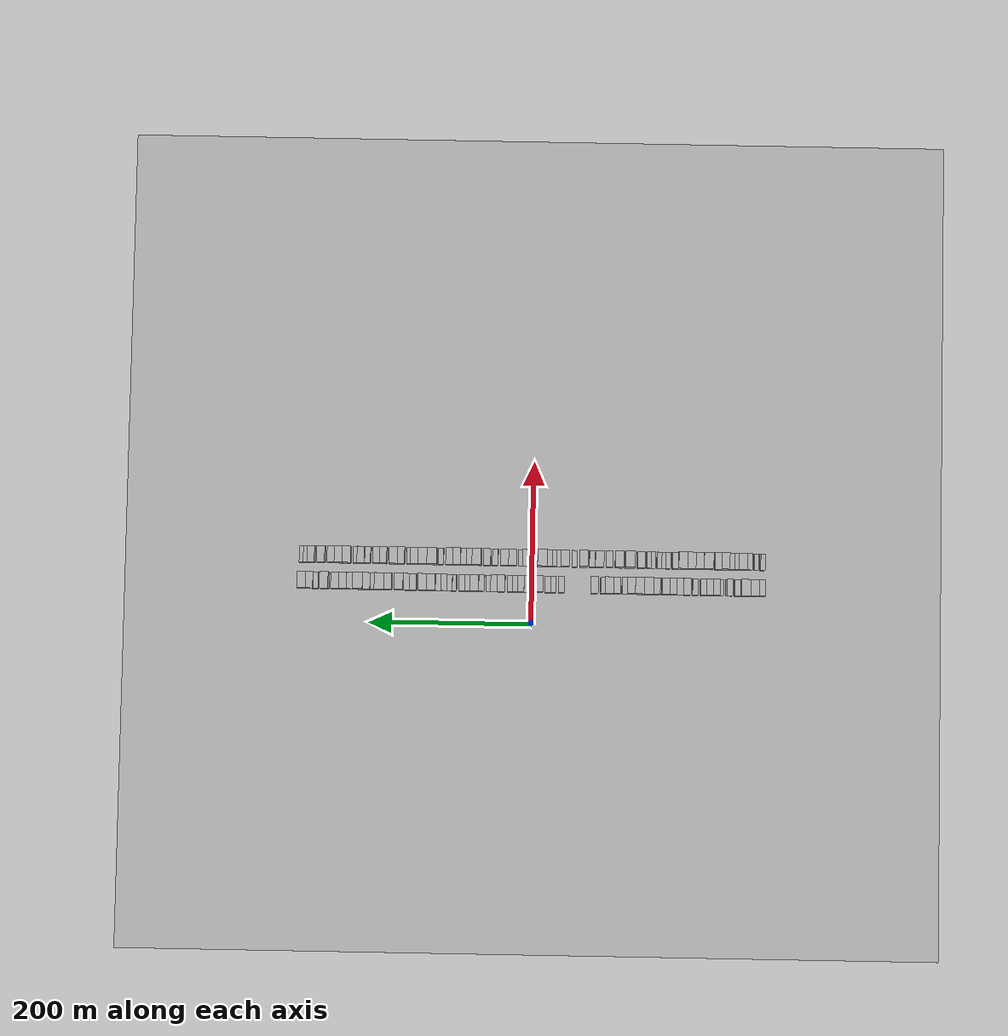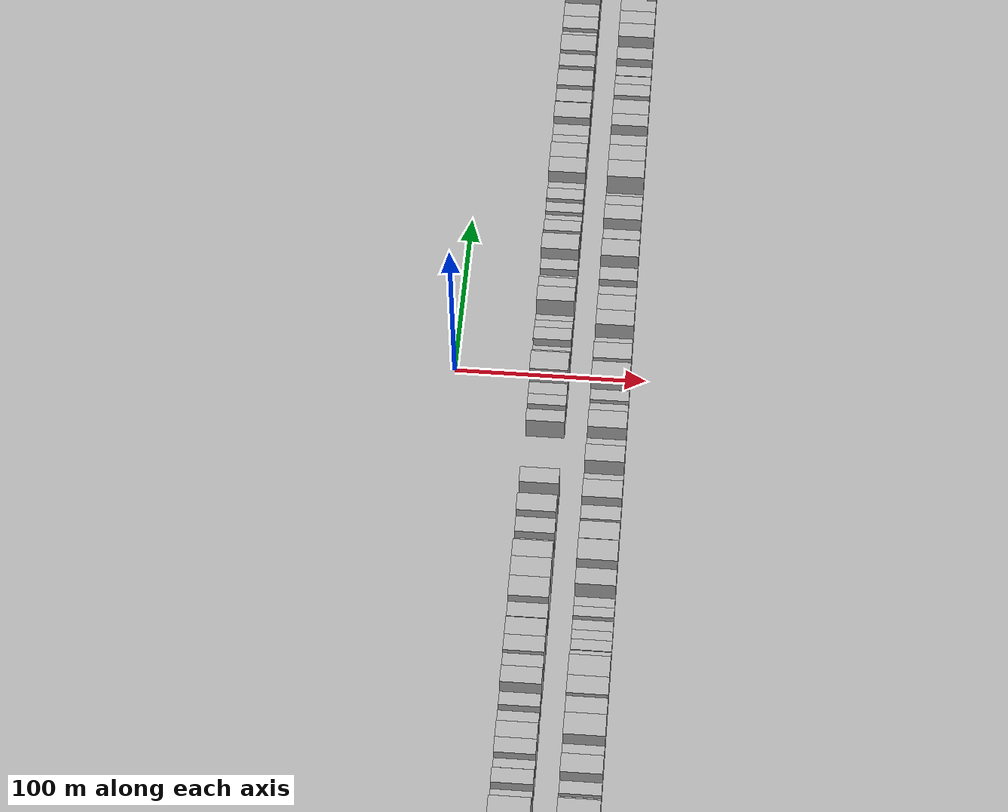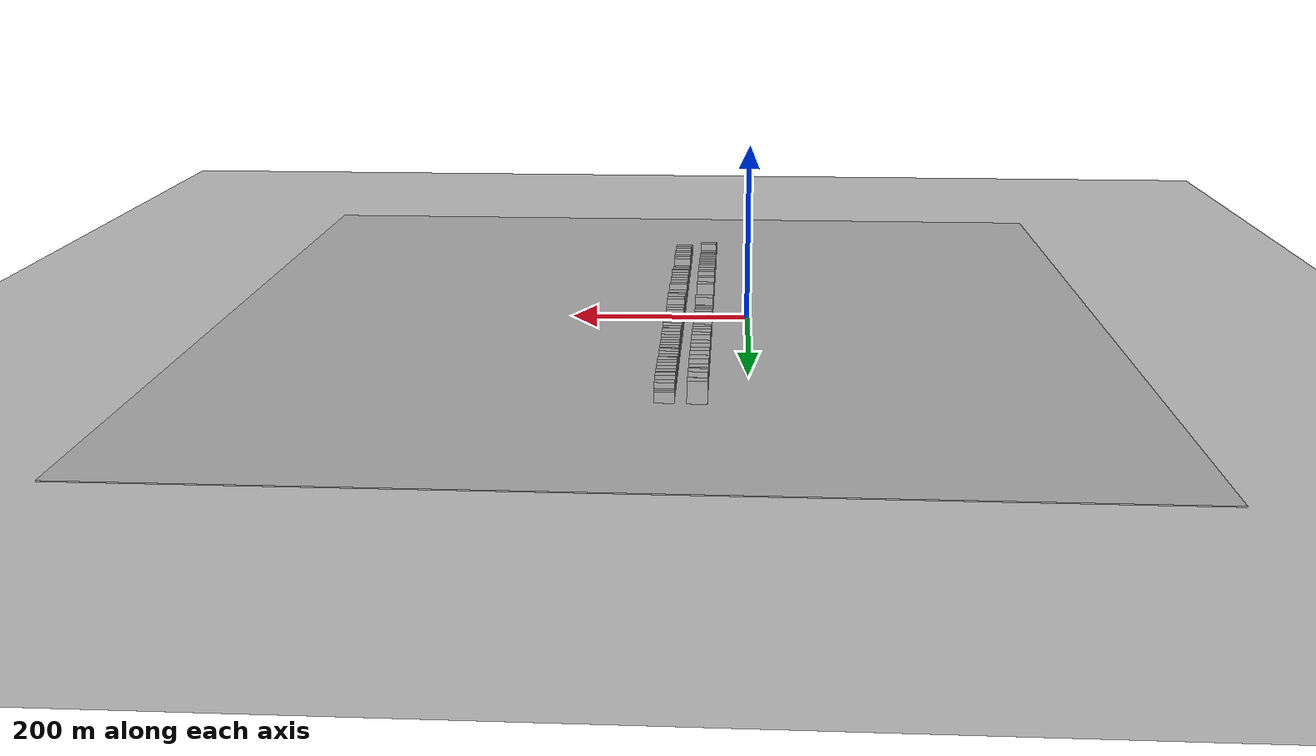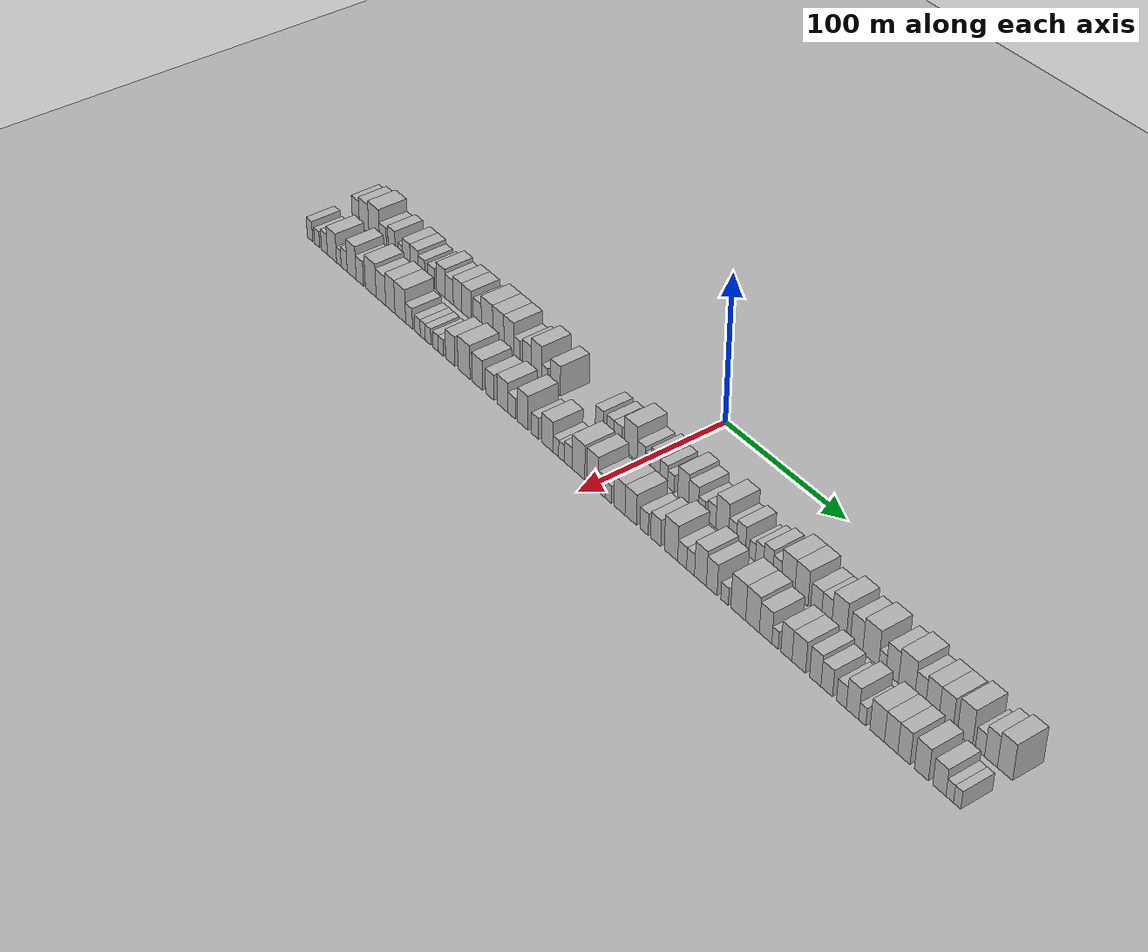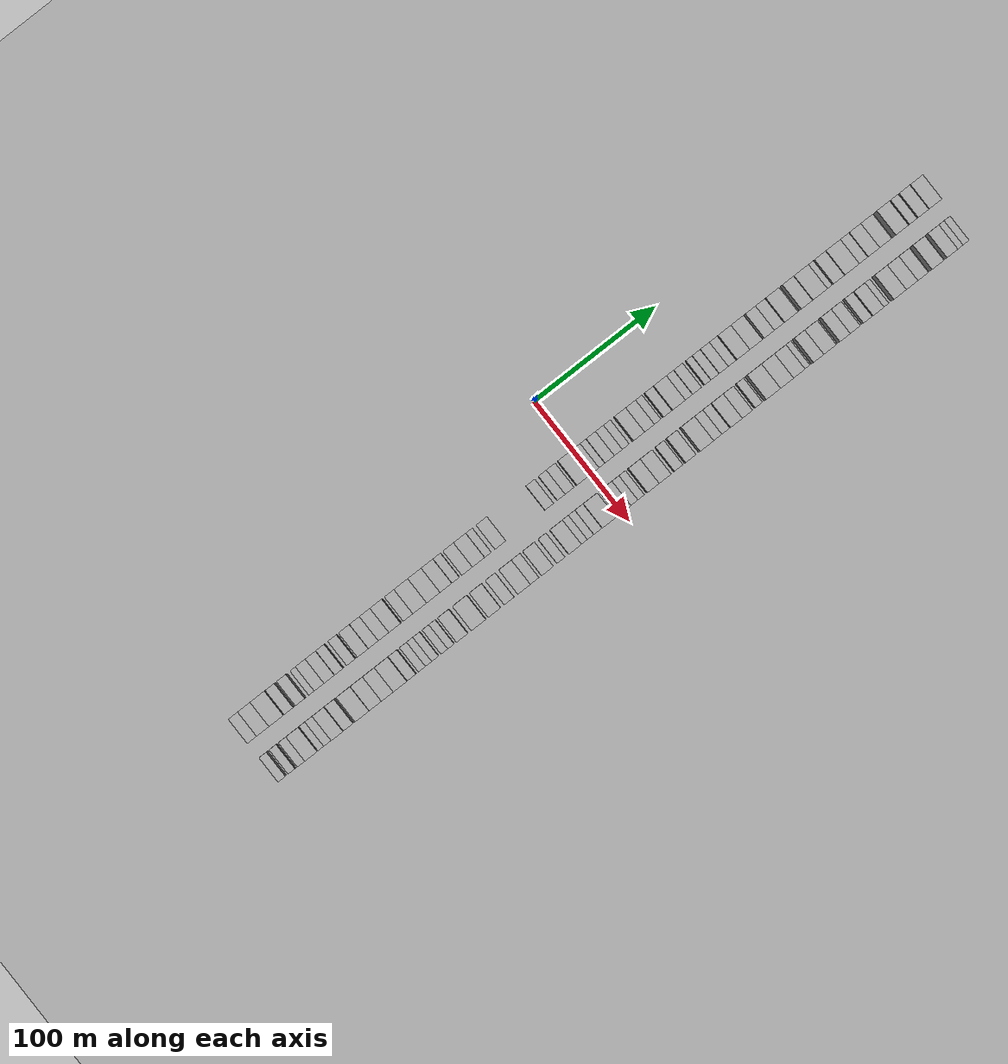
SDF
<?xml version="1.0" encoding="utf-8"?>

<sdf version="1.6">

   <world name="default">

      <gui fullscreen="0">

         <camera name="user_camera">

            <pose>-15 0 4.57585 0 0 0</pose>

            <view_controller>orbit</view_controller>

         </camera>

      </gui>

      <scene>

         <sky>

           <clouds>

             <speed>12</speed>

           </clouds>

         </sky>

         <ambient>0.4 0.4 0.4 1</ambient>

         <background>0.7 0.7 0.7 1</background>

         <shadows>1</shadows>

      </scene>

      <gravity>0 0 -9.8066</gravity>

      <magnetic_field>6e-06 2.3e-05 -4.2e-05</magnetic_field>

      <physics default="0" name="default_physics" type="ode">

         <ode>

            <solver>

               <type>quick</type>

               <iters>10</iters>

               <sor>1.0</sor>

               <use_dynamic_moi_rescaling>0</use_dynamic_moi_rescaling>

            </solver>

            <constraints>

               <cfm>0</cfm>

               <erp>0.2</erp>

               <contact_max_correcting_vel>100</contact_max_correcting_vel>

               <contact_surface_layer>0.001</contact_surface_layer>

            </constraints>

         </ode>

         <max_step_size>0.004</max_step_size>

         <real_time_factor>1</real_time_factor>

         <real_time_update_rate>250</real_time_update_rate>

      </physics>

      <light name="sun" type="directional">

         <cast_shadows>1</cast_shadows>

         <pose>0 0 10 0 0 0</pose>

         <diffuse>0.8 0.8 0.8 1</diffuse>

         <specular>0.2 0.2 0.2 1</specular>

         <attenuation>

            <range>1000</range>

            <constant>0.9</constant>

            <linear>0.01</linear>

            <quadratic>0.001</quadratic>

         </attenuation>

         <direction>-0.5 0.1 -0.9</direction>

      </light>

      <include>

         <name>ground_plane_1</name>

         <uri>model://HANNAS_ground_plane</uri>

         <pose>0 0 0  0 0 0</pose>

      </include>

      <include>

         <name>ground_plane_2</name>

         <uri>model://HANNAS_ground_plane</uri>

         <pose>100 0 0  0 0 0</pose>

      </include>

      <model name="building_1">

         <static>1</static>

         <pose frame="">50.0000 -280.0364 0 0.000000 0.000000 0.000000</pose>

         <link name="link">

            <pose frame="">0 0 9.00 0 0 0</pose>

            <collision name="collision">

               <geometry>

                  <box>

                     <size>20.0000 7.9272 18.0000</size>

                  </box>

               </geometry>

               <max_contacts>10</max_contacts>

               <surface>

                  <contact>

                     <ode/>

                  </contact>

                  <bounce/>

                  <friction>

                     <torsional>

                        <ode/>

                     </torsional>

                     <ode/>

                  </friction>

               </surface>

            </collision>

            <visual name="visual">

               <cast_shadows>0</cast_shadows>

               <geometry>

                  <box>

                     <size>20.0000 7.9272 18.0000</size>

                  </box>

               </geometry>

               <material>

                  <script>

                     <uri>model://HANNAS_wall/materials/scripts</uri>

                     <uri>model://HANNAS_wall/materials/textures</uri>

                     <name>vrc/HANNAS_wall</name>

                  </script>

               </material>

            </visual>

            <self_collide>0</self_collide>

            <enable_wind>0</enable_wind>

            <kinematic>0</kinematic>

         </link>

      </model>

      <model name="building_2">

         <static>1</static>

         <pose frame="">50.0000 -270.8760 0 0.000000 0.000000 0.000000</pose>

         <link name="link">

            <pose frame="">0 0 10.50 0 0 0</pose>

            <collision name="collision">

               <geometry>

                  <box>

                     <size>20.0000 10.3936 21.0000</size>

                  </box>

               </geometry>

               <max_contacts>10</max_contacts>

               <surface>

                  <contact>

                     <ode/>

                  </contact>

                  <bounce/>

                  <friction>

                     <torsional>

                        <ode/>

                     </torsional>

                     <ode/>

                  </friction>

               </surface>

            </collision>

            <visual name="visual">

               <cast_shadows>0</cast_shadows>

               <geometry>

                  <box>

                     <size>20.0000 10.3936 21.0000</size>

                  </box>

               </geometry>

               <material>

                  <script>

                     <uri>model://HANNAS_wall/materials/scripts</uri>

                     <uri>model://HANNAS_wall/materials/textures</uri>

                     <name>vrc/HANNAS_wall</name>

                  </script>

               </material>

            </visual>

            <self_collide>0</self_collide>

            <enable_wind>0</enable_wind>

            <kinematic>0</kinematic>

         </link>

      </model>

      <model name="building_3">

         <static>1</static>

         <pose frame="">50.0000 -259.7815 0 0.000000 0.000000 0.000000</pose>

         <link name="link">

            <pose frame="">0 0 12.00 0 0 0</pose>

            <collision name="collision">

               <geometry>

                  <box>

                     <size>20.0000 11.7954 24.0000</size>

                  </box>

               </geometry>

               <max_contacts>10</max_contacts>

               <surface>

                  <contact>

                     <ode/>

                  </contact>

                  <bounce/>

                  <friction>

                     <torsional>

                        <ode/>

                     </torsional>

                     <ode/>

                  </friction>

               </surface>

            </collision>

            <visual name="visual">

               <cast_shadows>0</cast_shadows>

               <geometry>

                  <box>

                     <size>20.0000 11.7954 24.0000</size>

                  </box>

               </geometry>

               <material>

                  <script>

                     <uri>model://HANNAS_wall/materials/scripts</uri>

                     <uri>model://HANNAS_wall/materials/textures</uri>

                     <name>vrc/HANNAS_wall</name>

                  </script>

               </material>

            </visual>

            <self_collide>0</self_collide>

            <enable_wind>0</enable_wind>

            <kinematic>0</kinematic>

         </link>

      </model>

      <model name="building_4">

         <static>1</static>

         <pose frame="">50.0000 -250.1484 0 0.000000 0.000000 0.000000</pose>

         <link name="link">

            <pose frame="">0 0 7.50 0 0 0</pose>

            <collision name="collision">

               <geometry>

                  <box>

                     <size>20.0000 7.4707 15.0000</size>

                  </box>

               </geometry>

               <max_contacts>10</max_contacts>

               <surface>

                  <contact>

                     <ode/>

                  </contact>

                  <bounce/>

                  <friction>

                     <torsional>

                        <ode/>

                     </torsional>

                     <ode/>

                  </friction>

               </surface>

            </collision>

            <visual name="visual">

               <cast_shadows>0</cast_shadows>

               <geometry>

                  <box>

                     <size>20.0000 7.4707 15.0000</size>

                  </box>

               </geometry>

               <material>

                  <script>

                     <uri>model://HANNAS_wall/materials/scripts</uri>

                     <uri>model://HANNAS_wall/materials/textures</uri>

                     <name>vrc/HANNAS_wall</name>

                  </script>

               </material>

            </visual>

            <self_collide>0</self_collide>

            <enable_wind>0</enable_wind>

            <kinematic>0</kinematic>

         </link>

      </model>

      <model name="building_5">

         <static>1</static>

         <pose frame="">50.0000 -240.5626 0 0.000000 0.000000 0.000000</pose>

         <link name="link">

            <pose frame="">0 0 9.00 0 0 0</pose>

            <collision name="collision">

               <geometry>

                  <box>

                     <size>20.0000 7.7009 18.0000</size>

                  </box>

               </geometry>

               <max_contacts>10</max_contacts>

               <surface>

                  <contact>

                     <ode/>

                  </contact>

                  <bounce/>

                  <friction>

                     <torsional>

                        <ode/>

                     </torsional>

                     <ode/>

                  </friction>

               </surface>

            </collision>

            <visual name="visual">

               <cast_shadows>0</cast_shadows>

               <geometry>

                  <box>

                     <size>20.0000 7.7009 18.0000</size>

                  </box>

               </geometry>

               <material>

                  <script>

                     <uri>model://HANNAS_wall/materials/scripts</uri>

                     <uri>model://HANNAS_wall/materials/textures</uri>

                     <name>vrc/HANNAS_wall</name>

                  </script>

               </material>

            </visual>

            <self_collide>0</self_collide>

            <enable_wind>0</enable_wind>

            <kinematic>0</kinematic>

         </link>

      </model>

      <model name="building_6">

         <static>1</static>

         <pose frame="">50.0000 -231.2862 0 0.000000 0.000000 0.000000</pose>

         <link name="link">

            <pose frame="">0 0 6.00 0 0 0</pose>

            <collision name="collision">

               <geometry>

                  <box>

                     <size>20.0000 4.8521 12.0000</size>

                  </box>

               </geometry>

               <max_contacts>10</max_contacts>

               <surface>

                  <contact>

                     <ode/>

                  </contact>

                  <bounce/>

                  <friction>

                     <torsional>

                        <ode/>

                     </torsional>

                     <ode/>

                  </friction>

               </surface>

            </collision>

            <visual name="visual">

               <cast_shadows>0</cast_shadows>

               <geometry>

                  <box>

                     <size>20.0000 4.8521 12.0000</size>

                  </box>

               </geometry>

               <material>

                  <script>

                     <uri>model://HANNAS_wall/materials/scripts</uri>

                     <uri>model://HANNAS_wall/materials/textures</uri>

                     <name>vrc/HANNAS_wall</name>

                  </script>

               </material>

            </visual>

            <self_collide>0</self_collide>

            <enable_wind>0</enable_wind>

            <kinematic>0</kinematic>

         </link>

      </model>

      <model name="building_7">

         <static>1</static>

         <pose frame="">50.0000 -224.8250 0 0.000000 0.000000 0.000000</pose>

         <link name="link">

            <pose frame="">0 0 9.00 0 0 0</pose>

            <collision name="collision">

               <geometry>

                  <box>

                     <size>20.0000 8.0703 18.0000</size>

                  </box>

               </geometry>

               <max_contacts>10</max_contacts>

               <surface>

                  <contact>

                     <ode/>

                  </contact>

                  <bounce/>

                  <friction>

                     <torsional>

                        <ode/>

                     </torsional>

                     <ode/>

                  </friction>

               </surface>

            </collision>

            <visual name="visual">

               <cast_shadows>0</cast_shadows>

               <geometry>

                  <box>

                     <size>20.0000 8.0703 18.0000</size>

                  </box>

               </geometry>

               <material>

                  <script>

                     <uri>model://HANNAS_wall/materials/scripts</uri>

                     <uri>model://HANNAS_wall/materials/textures</uri>

                     <name>vrc/HANNAS_wall</name>

                  </script>

               </material>

            </visual>

            <self_collide>0</self_collide>

            <enable_wind>0</enable_wind>

            <kinematic>0</kinematic>

         </link>

      </model>

      <model name="building_8">

         <static>1</static>

         <pose frame="">50.0000 -216.5220 0 0.000000 0.000000 0.000000</pose>

         <link name="link">

            <pose frame="">0 0 9.00 0 0 0</pose>

            <collision name="collision">

               <geometry>

                  <box>

                     <size>20.0000 8.5356 18.0000</size>

                  </box>

               </geometry>

               <max_contacts>10</max_contacts>

               <surface>

                  <contact>

                     <ode/>

                  </contact>

                  <bounce/>

                  <friction>

                     <torsional>

                        <ode/>

                     </torsional>

                     <ode/>

                  </friction>

               </surface>

            </collision>

            <visual name="visual">

               <cast_shadows>0</cast_shadows>

               <geometry>

                  <box>

                     <size>20.0000 8.5356 18.0000</size>

                  </box>

               </geometry>

               <material>

                  <script>

                     <uri>model://HANNAS_wall/materials/scripts</uri>

                     <uri>model://HANNAS_wall/materials/textures</uri>

                     <name>vrc/HANNAS_wall</name>

                  </script>

               </material>

            </visual>

            <self_collide>0</self_collide>

            <enable_wind>0</enable_wind>

            <kinematic>0</kinematic>

         </link>

      </model>

      <model name="building_9">

         <static>1</static>

         <pose frame="">50.0000 -208.7909 0 0.000000 0.000000 0.000000</pose>

         <link name="link">

            <pose frame="">0 0 7.50 0 0 0</pose>

            <collision name="collision">

               <geometry>

                  <box>

                     <size>20.0000 6.9267 15.0000</size>

                  </box>

               </geometry>

               <max_contacts>10</max_contacts>

               <surface>

                  <contact>

                     <ode/>

                  </contact>

                  <bounce/>

                  <friction>

                     <torsional>

                        <ode/>

                     </torsional>

                     <ode/>

                  </friction>

               </surface>

            </collision>

            <visual name="visual">

               <cast_shadows>0</cast_shadows>

               <geometry>

                  <box>

                     <size>20.0000 6.9267 15.0000</size>

                  </box>

               </geometry>

               <material>

                  <script>

                     <uri>model://HANNAS_wall/materials/scripts</uri>

                     <uri>model://HANNAS_wall/materials/textures</uri>

                     <name>vrc/HANNAS_wall</name>

                  </script>

               </material>

            </visual>

            <self_collide>0</self_collide>

            <enable_wind>0</enable_wind>

            <kinematic>0</kinematic>

         </link>

      </model>

      <model name="building_10">

         <static>1</static>

         <pose frame="">50.0000 -198.7944 0 0.000000 0.000000 0.000000</pose>

         <link name="link">

            <pose frame="">0 0 7.50 0 0 0</pose>

            <collision name="collision">

               <geometry>

                  <box>

                     <size>20.0000 7.0663 15.0000</size>

                  </box>

               </geometry>

               <max_contacts>10</max_contacts>

               <surface>

                  <contact>

                     <ode/>

                  </contact>

                  <bounce/>

                  <friction>

                     <torsional>

                        <ode/>

                     </torsional>

                     <ode/>

                  </friction>

               </surface>

            </collision>

            <visual name="visual">

               <cast_shadows>0</cast_shadows>

               <geometry>

                  <box>

                     <size>20.0000 7.0663 15.0000</size>

                  </box>

               </geometry>

               <material>

                  <script>

                     <uri>model://HANNAS_wall/materials/scripts</uri>

                     <uri>model://HANNAS_wall/materials/textures</uri>

                     <name>vrc/HANNAS_wall</name>

                  </script>

               </material>

            </visual>

            <self_collide>0</self_collide>

            <enable_wind>0</enable_wind>

            <kinematic>0</kinematic>

         </link>

      </model>

      <model name="building_11">

         <static>1</static>

         <pose frame="">50.0000 -188.7851 0 0.000000 0.000000 0.000000</pose>

         <link name="link">

            <pose frame="">0 0 10.50 0 0 0</pose>

            <collision name="collision">

               <geometry>

                  <box>

                     <size>20.0000 8.9523 21.0000</size>

                  </box>

               </geometry>

               <max_contacts>10</max_contacts>

               <surface>

                  <contact>

                     <ode/>

                  </contact>

                  <bounce/>

                  <friction>

                     <torsional>

                        <ode/>

                     </torsional>

                     <ode/>

                  </friction>

               </surface>

            </collision>

            <visual name="visual">

               <cast_shadows>0</cast_shadows>

               <geometry>

                  <box>

                     <size>20.0000 8.9523 21.0000</size>

                  </box>

               </geometry>

               <material>

                  <script>

                     <uri>model://HANNAS_wall/materials/scripts</uri>

                     <uri>model://HANNAS_wall/materials/textures</uri>

                     <name>vrc/HANNAS_wall</name>

                  </script>

               </material>

            </visual>

            <self_collide>0</self_collide>

            <enable_wind>0</enable_wind>

            <kinematic>0</kinematic>

         </link>

      </model>

      <model name="building_12">

         <static>1</static>

         <pose frame="">50.0000 -180.1561 0 0.000000 0.000000 0.000000</pose>

         <link name="link">

            <pose frame="">0 0 9.00 0 0 0</pose>

            <collision name="collision">

               <geometry>

                  <box>

                     <size>20.0000 8.3055 18.0000</size>

                  </box>

               </geometry>

               <max_contacts>10</max_contacts>

               <surface>

                  <contact>

                     <ode/>

                  </contact>

                  <bounce/>

                  <friction>

                     <torsional>

                        <ode/>

                     </torsional>

                     <ode/>

                  </friction>

               </surface>

            </collision>

            <visual name="visual">

               <cast_shadows>0</cast_shadows>

               <geometry>

                  <box>

                     <size>20.0000 8.3055 18.0000</size>

                  </box>

               </geometry>

               <material>

                  <script>

                     <uri>model://HANNAS_wall/materials/scripts</uri>

                     <uri>model://HANNAS_wall/materials/textures</uri>

                     <name>vrc/HANNAS_wall</name>

                  </script>

               </material>

            </visual>

            <self_collide>0</self_collide>

            <enable_wind>0</enable_wind>

            <kinematic>0</kinematic>

         </link>

      </model>

      <model name="building_13">

         <static>1</static>

         <pose frame="">50.0000 -171.6764 0 0.000000 0.000000 0.000000</pose>

         <link name="link">

            <pose frame="">0 0 10.50 0 0 0</pose>

            <collision name="collision">

               <geometry>

                  <box>

                     <size>20.0000 8.6539 21.0000</size>

                  </box>

               </geometry>

               <max_contacts>10</max_contacts>

               <surface>

                  <contact>

                     <ode/>

                  </contact>

                  <bounce/>

                  <friction>

                     <torsional>

                        <ode/>

                     </torsional>

                     <ode/>

                  </friction>

               </surface>

            </collision>

            <visual name="visual">

               <cast_shadows>0</cast_shadows>

               <geometry>

                  <box>

                     <size>20.0000 8.6539 21.0000</size>

                  </box>

               </geometry>

               <material>

                  <script>

                     <uri>model://HANNAS_wall/materials/scripts</uri>

                     <uri>model://HANNAS_wall/materials/textures</uri>

                     <name>vrc/HANNAS_wall</name>

                  </script>

               </material>

            </visual>

            <self_collide>0</self_collide>

            <enable_wind>0</enable_wind>

            <kinematic>0</kinematic>

         </link>

      </model>

      <model name="building_14">

         <static>1</static>

         <pose frame="">50.0000 -162.4909 0 0.000000 0.000000 0.000000</pose>

         <link name="link">

            <pose frame="">0 0 10.50 0 0 0</pose>

            <collision name="collision">

               <geometry>

                  <box>

                     <size>20.0000 9.7172 21.0000</size>

                  </box>

               </geometry>

               <max_contacts>10</max_contacts>

               <surface>

                  <contact>

                     <ode/>

                  </contact>

                  <bounce/>

                  <friction>

                     <torsional>

                        <ode/>

                     </torsional>

                     <ode/>

                  </friction>

               </surface>

            </collision>

            <visual name="visual">

               <cast_shadows>0</cast_shadows>

               <geometry>

                  <box>

                     <size>20.0000 9.7172 21.0000</size>

                  </box>

               </geometry>

               <material>

                  <script>

                     <uri>model://HANNAS_wall/materials/scripts</uri>

                     <uri>model://HANNAS_wall/materials/textures</uri>

                     <name>vrc/HANNAS_wall</name>

                  </script>

               </material>

            </visual>

            <self_collide>0</self_collide>

            <enable_wind>0</enable_wind>

            <kinematic>0</kinematic>

         </link>

      </model>

      <model name="building_15">

         <static>1</static>

         <pose frame="">50.0000 -151.5765 0 0.000000 0.000000 0.000000</pose>

         <link name="link">

            <pose frame="">0 0 9.00 0 0 0</pose>

            <collision name="collision">

               <geometry>

                  <box>

                     <size>20.0000 8.1117 18.0000</size>

                  </box>

               </geometry>

               <max_contacts>10</max_contacts>

               <surface>

                  <contact>

                     <ode/>

                  </contact>

                  <bounce/>

                  <friction>

                     <torsional>

                        <ode/>

                     </torsional>

                     <ode/>

                  </friction>

               </surface>

            </collision>

            <visual name="visual">

               <cast_shadows>0</cast_shadows>

               <geometry>

                  <box>

                     <size>20.0000 8.1117 18.0000</size>

                  </box>

               </geometry>

               <material>

                  <script>

                     <uri>model://HANNAS_wall/materials/scripts</uri>

                     <uri>model://HANNAS_wall/materials/textures</uri>

                     <name>vrc/HANNAS_wall</name>

                  </script>

               </material>

            </visual>

            <self_collide>0</self_collide>

            <enable_wind>0</enable_wind>

            <kinematic>0</kinematic>

         </link>

      </model>

      <model name="building_16">

         <static>1</static>

         <pose frame="">50.0000 -141.8752 0 0.000000 0.000000 0.000000</pose>

         <link name="link">

            <pose frame="">0 0 12.00 0 0 0</pose>

            <collision name="collision">

               <geometry>

                  <box>

                     <size>20.0000 11.2909 24.0000</size>

                  </box>

               </geometry>

               <max_contacts>10</max_contacts>

               <surface>

                  <contact>

                     <ode/>

                  </contact>

                  <bounce/>

                  <friction>

                     <torsional>

                        <ode/>

                     </torsional>

                     <ode/>

                  </friction>

               </surface>

            </collision>

            <visual name="visual">

               <cast_shadows>0</cast_shadows>

               <geometry>

                  <box>

                     <size>20.0000 11.2909 24.0000</size>

                  </box>

               </geometry>

               <material>

                  <script>

                     <uri>model://HANNAS_wall/materials/scripts</uri>

                     <uri>model://HANNAS_wall/materials/textures</uri>

                     <name>vrc/HANNAS_wall</name>

                  </script>

               </material>

            </visual>

            <self_collide>0</self_collide>

            <enable_wind>0</enable_wind>

            <kinematic>0</kinematic>

         </link>

      </model>

      <model name="building_17">

         <static>1</static>

         <pose frame="">50.0000 -130.7144 0 0.000000 0.000000 0.000000</pose>

         <link name="link">

            <pose frame="">0 0 12.00 0 0 0</pose>

            <collision name="collision">

               <geometry>

                  <box>

                     <size>20.0000 11.0307 24.0000</size>

                  </box>

               </geometry>

               <max_contacts>10</max_contacts>

               <surface>

                  <contact>

                     <ode/>

                  </contact>

                  <bounce/>

                  <friction>

                     <torsional>

                        <ode/>

                     </torsional>

                     <ode/>

                  </friction>

               </surface>

            </collision>

            <visual name="visual">

               <cast_shadows>0</cast_shadows>

               <geometry>

                  <box>

                     <size>20.0000 11.0307 24.0000</size>

                  </box>

               </geometry>

               <material>

                  <script>

                     <uri>model://HANNAS_wall/materials/scripts</uri>

                     <uri>model://HANNAS_wall/materials/textures</uri>

                     <name>vrc/HANNAS_wall</name>

                  </script>

               </material>

            </visual>

            <self_collide>0</self_collide>

            <enable_wind>0</enable_wind>

            <kinematic>0</kinematic>

         </link>

      </model>

      <model name="building_18">

         <static>1</static>

         <pose frame="">50.0000 -120.3880 0 0.000000 0.000000 0.000000</pose>

         <link name="link">

            <pose frame="">0 0 12.00 0 0 0</pose>

            <collision name="collision">

               <geometry>

                  <box>

                     <size>20.0000 9.6219 24.0000</size>

                  </box>

               </geometry>

               <max_contacts>10</max_contacts>

               <surface>

                  <contact>

                     <ode/>

                  </contact>

                  <bounce/>

                  <friction>

                     <torsional>

                        <ode/>

                     </torsional>

                     <ode/>

                  </friction>

               </surface>

            </collision>

            <visual name="visual">

               <cast_shadows>0</cast_shadows>

               <geometry>

                  <box>

                     <size>20.0000 9.6219 24.0000</size>

                  </box>

               </geometry>

               <material>

                  <script>

                     <uri>model://HANNAS_wall/materials/scripts</uri>

                     <uri>model://HANNAS_wall/materials/textures</uri>

                     <name>vrc/HANNAS_wall</name>

                  </script>

               </material>

            </visual>

            <self_collide>0</self_collide>

            <enable_wind>0</enable_wind>

            <kinematic>0</kinematic>

         </link>

      </model>

      <model name="building_19">

         <static>1</static>

         <pose frame="">50.0000 -112.5181 0 0.000000 0.000000 0.000000</pose>

         <link name="link">

            <pose frame="">0 0 7.50 0 0 0</pose>

            <collision name="collision">

               <geometry>

                  <box>

                     <size>20.0000 6.1178 15.0000</size>

                  </box>

               </geometry>

               <max_contacts>10</max_contacts>

               <surface>

                  <contact>

                     <ode/>

                  </contact>

                  <bounce/>

                  <friction>

                     <torsional>

                        <ode/>

                     </torsional>

                     <ode/>

                  </friction>

               </surface>

            </collision>

            <visual name="visual">

               <cast_shadows>0</cast_shadows>

               <geometry>

                  <box>

                     <size>20.0000 6.1178 15.0000</size>

                  </box>

               </geometry>

               <material>

                  <script>

                     <uri>model://HANNAS_wall/materials/scripts</uri>

                     <uri>model://HANNAS_wall/materials/textures</uri>

                     <name>vrc/HANNAS_wall</name>

                  </script>

               </material>

            </visual>

            <self_collide>0</self_collide>

            <enable_wind>0</enable_wind>

            <kinematic>0</kinematic>

         </link>

      </model>

      <model name="building_20">

         <static>1</static>

         <pose frame="">50.0000 -103.0494 0 0.000000 0.000000 0.000000</pose>

         <link name="link">

            <pose frame="">0 0 9.00 0 0 0</pose>

            <collision name="collision">

               <geometry>

                  <box>

                     <size>20.0000 8.8197 18.0000</size>

                  </box>

               </geometry>

               <max_contacts>10</max_contacts>

               <surface>

                  <contact>

                     <ode/>

                  </contact>

                  <bounce/>

                  <friction>

                     <torsional>

                        <ode/>

                     </torsional>

                     <ode/>

                  </friction>

               </surface>

            </collision>

            <visual name="visual">

               <cast_shadows>0</cast_shadows>

               <geometry>

                  <box>

                     <size>20.0000 8.8197 18.0000</size>

                  </box>

               </geometry>

               <material>

                  <script>

                     <uri>model://HANNAS_wall/materials/scripts</uri>

                     <uri>model://HANNAS_wall/materials/textures</uri>

                     <name>vrc/HANNAS_wall</name>

                  </script>

               </material>

            </visual>

            <self_collide>0</self_collide>

            <enable_wind>0</enable_wind>

            <kinematic>0</kinematic>

         </link>

      </model>

      <model name="building_21">

         <static>1</static>

         <pose frame="">50.0000 -93.6185 0 0.000000 0.000000 0.000000</pose>

         <link name="link">

            <pose frame="">0 0 12.00 0 0 0</pose>

            <collision name="collision">

               <geometry>

                  <box>

                     <size>20.0000 10.0421 24.0000</size>

                  </box>

               </geometry>

               <max_contacts>10</max_contacts>

               <surface>

                  <contact>

                     <ode/>

                  </contact>

                  <bounce/>

                  <friction>

                     <torsional>

                        <ode/>

                     </torsional>

                     <ode/>

                  </friction>

               </surface>

            </collision>

            <visual name="visual">

               <cast_shadows>0</cast_shadows>

               <geometry>

                  <box>

                     <size>20.0000 10.0421 24.0000</size>

                  </box>

               </geometry>

               <material>

                  <script>

                     <uri>model://HANNAS_wall/materials/scripts</uri>

                     <uri>model://HANNAS_wall/materials/textures</uri>

                     <name>vrc/HANNAS_wall</name>

                  </script>

               </material>

            </visual>

            <self_collide>0</self_collide>

            <enable_wind>0</enable_wind>

            <kinematic>0</kinematic>

         </link>

      </model>

      <model name="building_22">

         <static>1</static>

         <pose frame="">50.0000 -85.8899 0 0.000000 0.000000 0.000000</pose>

         <link name="link">

            <pose frame="">0 0 6.00 0 0 0</pose>

            <collision name="collision">

               <geometry>

                  <box>

                     <size>20.0000 5.4150 12.0000</size>

                  </box>

               </geometry>

               <max_contacts>10</max_contacts>

               <surface>

                  <contact>

                     <ode/>

                  </contact>

                  <bounce/>

                  <friction>

                     <torsional>

                        <ode/>

                     </torsional>

                     <ode/>

                  </friction>

               </surface>

            </collision>

            <visual name="visual">

               <cast_shadows>0</cast_shadows>

               <geometry>

                  <box>

                     <size>20.0000 5.4150 12.0000</size>

                  </box>

               </geometry>

               <material>

                  <script>

                     <uri>model://HANNAS_wall/materials/scripts</uri>

                     <uri>model://HANNAS_wall/materials/textures</uri>

                     <name>vrc/HANNAS_wall</name>

                  </script>

               </material>

            </visual>

            <self_collide>0</self_collide>

            <enable_wind>0</enable_wind>

            <kinematic>0</kinematic>

         </link>

      </model>

      <model name="building_23">

         <static>1</static>

         <pose frame="">50.0000 -75.6865 0 0.000000 0.000000 0.000000</pose>

         <link name="link">

            <pose frame="">0 0 10.50 0 0 0</pose>

            <collision name="collision">

               <geometry>

                  <box>

                     <size>20.0000 8.9918 21.0000</size>

                  </box>

               </geometry>

               <max_contacts>10</max_contacts>

               <surface>

                  <contact>

                     <ode/>

                  </contact>

                  <bounce/>

                  <friction>

                     <torsional>

                        <ode/>

                     </torsional>

                     <ode/>

                  </friction>

               </surface>

            </collision>

            <visual name="visual">

               <cast_shadows>0</cast_shadows>

               <geometry>

                  <box>

                     <size>20.0000 8.9918 21.0000</size>

                  </box>

               </geometry>

               <material>

                  <script>

                     <uri>model://HANNAS_wall/materials/scripts</uri>

                     <uri>model://HANNAS_wall/materials/textures</uri>

                     <name>vrc/HANNAS_wall</name>

                  </script>

               </material>

            </visual>

            <self_collide>0</self_collide>

            <enable_wind>0</enable_wind>

            <kinematic>0</kinematic>

         </link>

      </model>

      <model name="building_24">

         <static>1</static>

         <pose frame="">50.0000 -35.3655 0 0.000000 0.000000 0.000000</pose>

         <link name="link">

            <pose frame="">0 0 7.50 0 0 0</pose>

            <collision name="collision">

               <geometry>

                  <box>

                     <size>20.0000 7.2167 15.0000</size>

                  </box>

               </geometry>

               <max_contacts>10</max_contacts>

               <surface>

                  <contact>

                     <ode/>

                  </contact>

                  <bounce/>

                  <friction>

                     <torsional>

                        <ode/>

                     </torsional>

                     <ode/>

                  </friction>

               </surface>

            </collision>

            <visual name="visual">

               <cast_shadows>0</cast_shadows>

               <geometry>

                  <box>

                     <size>20.0000 7.2167 15.0000</size>

                  </box>

               </geometry>

               <material>

                  <script>

                     <uri>model://HANNAS_wall/materials/scripts</uri>

                     <uri>model://HANNAS_wall/materials/textures</uri>

                     <name>vrc/HANNAS_wall</name>

                  </script>

               </material>

            </visual>

            <self_collide>0</self_collide>

            <enable_wind>0</enable_wind>

            <kinematic>0</kinematic>

         </link>

      </model>

      <model name="building_25">

         <static>1</static>

         <pose frame="">50.0000 -25.5118 0 0.000000 0.000000 0.000000</pose>

         <link name="link">

            <pose frame="">0 0 7.50 0 0 0</pose>

            <collision name="collision">

               <geometry>

                  <box>

                     <size>20.0000 6.4908 15.0000</size>

                  </box>

               </geometry>

               <max_contacts>10</max_contacts>

               <surface>

                  <contact>

                     <ode/>

                  </contact>

                  <bounce/>

                  <friction>

                     <torsional>

                        <ode/>

                     </torsional>

                     <ode/>

                  </friction>

               </surface>

            </collision>

            <visual name="visual">

               <cast_shadows>0</cast_shadows>

               <geometry>

                  <box>

                     <size>20.0000 6.4908 15.0000</size>

                  </box>

               </geometry>

               <material>

                  <script>

                     <uri>model://HANNAS_wall/materials/scripts</uri>

                     <uri>model://HANNAS_wall/materials/textures</uri>

                     <name>vrc/HANNAS_wall</name>

                  </script>

               </material>

            </visual>

            <self_collide>0</self_collide>

            <enable_wind>0</enable_wind>

            <kinematic>0</kinematic>

         </link>

      </model>

      <model name="building_26">

         <static>1</static>

         <pose frame="">50.0000 -18.5920 0 0.000000 0.000000 0.000000</pose>

         <link name="link">

            <pose frame="">0 0 7.50 0 0 0</pose>

            <collision name="collision">

               <geometry>

                  <box>

                     <size>20.0000 7.3487 15.0000</size>

                  </box>

               </geometry>

               <max_contacts>10</max_contacts>

               <surface>

                  <contact>

                     <ode/>

                  </contact>

                  <bounce/>

                  <friction>

                     <torsional>

                        <ode/>

                     </torsional>

                     <ode/>

                  </friction>

               </surface>

            </collision>

            <visual name="visual">

               <cast_shadows>0</cast_shadows>

               <geometry>

                  <box>

                     <size>20.0000 7.3487 15.0000</size>

                  </box>

               </geometry>

               <material>

                  <script>

                     <uri>model://HANNAS_wall/materials/scripts</uri>

                     <uri>model://HANNAS_wall/materials/textures</uri>

                     <name>vrc/HANNAS_wall</name>

                  </script>

               </material>

            </visual>

            <self_collide>0</self_collide>

            <enable_wind>0</enable_wind>

            <kinematic>0</kinematic>

         </link>

      </model>

      <model name="building_27">

         <static>1</static>

         <pose frame="">50.0000 -7.2226 0 0.000000 0.000000 0.000000</pose>

         <link name="link">

            <pose frame="">0 0 12.00 0 0 0</pose>

            <collision name="collision">

               <geometry>

                  <box>

                     <size>20.0000 11.3902 24.0000</size>

                  </box>

               </geometry>

               <max_contacts>10</max_contacts>

               <surface>

                  <contact>

                     <ode/>

                  </contact>

                  <bounce/>

                  <friction>

                     <torsional>

                        <ode/>

                     </torsional>

                     <ode/>

                  </friction>

               </surface>

            </collision>

            <visual name="visual">

               <cast_shadows>0</cast_shadows>

               <geometry>

                  <box>

                     <size>20.0000 11.3902 24.0000</size>

                  </box>

               </geometry>

               <material>

                  <script>

                     <uri>model://HANNAS_wall/materials/scripts</uri>

                     <uri>model://HANNAS_wall/materials/textures</uri>

                     <name>vrc/HANNAS_wall</name>

                  </script>

               </material>

            </visual>

            <self_collide>0</self_collide>

            <enable_wind>0</enable_wind>

            <kinematic>0</kinematic>

         </link>

      </model>

      <model name="building_28">

         <static>1</static>

         <pose frame="">50.0000 2.0500 0 0.000000 0.000000 0.000000</pose>

         <link name="link">

            <pose frame="">0 0 7.50 0 0 0</pose>

            <collision name="collision">

               <geometry>

                  <box>

                     <size>20.0000 7.1551 15.0000</size>

                  </box>

               </geometry>

               <max_contacts>10</max_contacts>

               <surface>

                  <contact>

                     <ode/>

                  </contact>

                  <bounce/>

                  <friction>

                     <torsional>

                        <ode/>

                     </torsional>

                     <ode/>

                  </friction>

               </surface>

            </collision>

            <visual name="visual">

               <cast_shadows>0</cast_shadows>

               <geometry>

                  <box>

                     <size>20.0000 7.1551 15.0000</size>

                  </box>

               </geometry>

               <material>

                  <script>

                     <uri>model://HANNAS_wall/materials/scripts</uri>

                     <uri>model://HANNAS_wall/materials/textures</uri>

                     <name>vrc/HANNAS_wall</name>

                  </script>

               </material>

            </visual>

            <self_collide>0</self_collide>

            <enable_wind>0</enable_wind>

            <kinematic>0</kinematic>

         </link>

      </model>

      <model name="building_29">

         <static>1</static>

         <pose frame="">50.0000 8.0518 0 0.000000 0.000000 0.000000</pose>

         <link name="link">

            <pose frame="">0 0 6.00 0 0 0</pose>

            <collision name="collision">

               <geometry>

                  <box>

                     <size>20.0000 4.8486 12.0000</size>

                  </box>

               </geometry>

               <max_contacts>10</max_contacts>

               <surface>

                  <contact>

                     <ode/>

                  </contact>

                  <bounce/>

                  <friction>

                     <torsional>

                        <ode/>

                     </torsional>

                     <ode/>

                  </friction>

               </surface>

            </collision>

            <visual name="visual">

               <cast_shadows>0</cast_shadows>

               <geometry>

                  <box>

                     <size>20.0000 4.8486 12.0000</size>

                  </box>

               </geometry>

               <material>

                  <script>

                     <uri>model://HANNAS_wall/materials/scripts</uri>

                     <uri>model://HANNAS_wall/materials/textures</uri>

                     <name>vrc/HANNAS_wall</name>

                  </script>

               </material>

            </visual>

            <self_collide>0</self_collide>

            <enable_wind>0</enable_wind>

            <kinematic>0</kinematic>

         </link>

      </model>

      <model name="building_30">

         <static>1</static>

         <pose frame="">50.0000 14.3222 0 0.000000 0.000000 0.000000</pose>

         <link name="link">

            <pose frame="">0 0 9.00 0 0 0</pose>

            <collision name="collision">

               <geometry>

                  <box>

                     <size>20.0000 7.6922 18.0000</size>

                  </box>

               </geometry>

               <max_contacts>10</max_contacts>

               <surface>

                  <contact>

                     <ode/>

                  </contact>

                  <bounce/>

                  <friction>

                     <torsional>

                        <ode/>

                     </torsional>

                     <ode/>

                  </friction>

               </surface>

            </collision>

            <visual name="visual">

               <cast_shadows>0</cast_shadows>

               <geometry>

                  <box>

                     <size>20.0000 7.6922 18.0000</size>

                  </box>

               </geometry>

               <material>

                  <script>

                     <uri>model://HANNAS_wall/materials/scripts</uri>

                     <uri>model://HANNAS_wall/materials/textures</uri>

                     <name>vrc/HANNAS_wall</name>

                  </script>

               </material>

            </visual>

            <self_collide>0</self_collide>

            <enable_wind>0</enable_wind>

            <kinematic>0</kinematic>

         </link>

      </model>

      <model name="building_31">

         <static>1</static>

         <pose frame="">50.0000 21.5306 0 0.000000 0.000000 0.000000</pose>

         <link name="link">

            <pose frame="">0 0 7.50 0 0 0</pose>

            <collision name="collision">

               <geometry>

                  <box>

                     <size>20.0000 6.7246 15.0000</size>

                  </box>

               </geometry>

               <max_contacts>10</max_contacts>

               <surface>

                  <contact>

                     <ode/>

                  </contact>

                  <bounce/>

                  <friction>

                     <torsional>

                        <ode/>

                     </torsional>

                     <ode/>

                  </friction>

               </surface>

            </collision>

            <visual name="visual">

               <cast_shadows>0</cast_shadows>

               <geometry>

                  <box>

                     <size>20.0000 6.7246 15.0000</size>

                  </box>

               </geometry>

               <material>

                  <script>

                     <uri>model://HANNAS_wall/materials/scripts</uri>

                     <uri>model://HANNAS_wall/materials/textures</uri>

                     <name>vrc/HANNAS_wall</name>

                  </script>

               </material>

            </visual>

            <self_collide>0</self_collide>

            <enable_wind>0</enable_wind>

            <kinematic>0</kinematic>

         </link>

      </model>

      <model name="building_32">

         <static>1</static>

         <pose frame="">50.0000 27.7920 0 0.000000 0.000000 0.000000</pose>

         <link name="link">

            <pose frame="">0 0 6.00 0 0 0</pose>

            <collision name="collision">

               <geometry>

                  <box>

                     <size>20.0000 5.7983 12.0000</size>

                  </box>

               </geometry>

               <max_contacts>10</max_contacts>

               <surface>

                  <contact>

                     <ode/>

                  </contact>

                  <bounce/>

                  <friction>

                     <torsional>

                        <ode/>

                     </torsional>

                     <ode/>

                  </friction>

               </surface>

            </collision>

            <visual name="visual">

               <cast_shadows>0</cast_shadows>

               <geometry>

                  <box>

                     <size>20.0000 5.7983 12.0000</size>

                  </box>

               </geometry>

               <material>

                  <script>

                     <uri>model://HANNAS_wall/materials/scripts</uri>

                     <uri>model://HANNAS_wall/materials/textures</uri>

                     <name>vrc/HANNAS_wall</name>

                  </script>

               </material>

            </visual>

            <self_collide>0</self_collide>

            <enable_wind>0</enable_wind>

            <kinematic>0</kinematic>

         </link>

      </model>

      <model name="building_33">

         <static>1</static>

         <pose frame="">50.0000 38.2990 0 0.000000 0.000000 0.000000</pose>

         <link name="link">

            <pose frame="">0 0 10.50 0 0 0</pose>

            <collision name="collision">

               <geometry>

                  <box>

                     <size>20.0000 9.2155 21.0000</size>

                  </box>

               </geometry>

               <max_contacts>10</max_contacts>

               <surface>

                  <contact>

                     <ode/>

                  </contact>

                  <bounce/>

                  <friction>

                     <torsional>

                        <ode/>

                     </torsional>

                     <ode/>

                  </friction>

               </surface>

            </collision>

            <visual name="visual">

               <cast_shadows>0</cast_shadows>

               <geometry>

                  <box>

                     <size>20.0000 9.2155 21.0000</size>

                  </box>

               </geometry>

               <material>

                  <script>

                     <uri>model://HANNAS_wall/materials/scripts</uri>

                     <uri>model://HANNAS_wall/materials/textures</uri>

                     <name>vrc/HANNAS_wall</name>

                  </script>

               </material>

            </visual>

            <self_collide>0</self_collide>

            <enable_wind>0</enable_wind>

            <kinematic>0</kinematic>

         </link>

      </model>

      <model name="building_34">

         <static>1</static>

         <pose frame="">50.0000 47.0198 0 0.000000 0.000000 0.000000</pose>

         <link name="link">

            <pose frame="">0 0 9.00 0 0 0</pose>

            <collision name="collision">

               <geometry>

                  <box>

                     <size>20.0000 8.2262 18.0000</size>

                  </box>

               </geometry>

               <max_contacts>10</max_contacts>

               <surface>

                  <contact>

                     <ode/>

                  </contact>

                  <bounce/>

                  <friction>

                     <torsional>

                        <ode/>

                     </torsional>

                     <ode/>

                  </friction>

               </surface>

            </collision>

            <visual name="visual">

               <cast_shadows>0</cast_shadows>

               <geometry>

                  <box>

                     <size>20.0000 8.2262 18.0000</size>

                  </box>

               </geometry>

               <material>

                  <script>

                     <uri>model://HANNAS_wall/materials/scripts</uri>

                     <uri>model://HANNAS_wall/materials/textures</uri>

                     <name>vrc/HANNAS_wall</name>

                  </script>

               </material>

            </visual>

            <self_collide>0</self_collide>

            <enable_wind>0</enable_wind>

            <kinematic>0</kinematic>

         </link>

      </model>

      <model name="building_35">

         <static>1</static>

         <pose frame="">50.0000 53.9858 0 0.000000 0.000000 0.000000</pose>

         <link name="link">

            <pose frame="">0 0 6.00 0 0 0</pose>

            <collision name="collision">

               <geometry>

                  <box>

                     <size>20.0000 5.7058 12.0000</size>

                  </box>

               </geometry>

               <max_contacts>10</max_contacts>

               <surface>

                  <contact>

                     <ode/>

                  </contact>

                  <bounce/>

                  <friction>

                     <torsional>

                        <ode/>

                     </torsional>

                     <ode/>

                  </friction>

               </surface>

            </collision>

            <visual name="visual">

               <cast_shadows>0</cast_shadows>

               <geometry>

                  <box>

                     <size>20.0000 5.7058 12.0000</size>

                  </box>

               </geometry>

               <material>

                  <script>

                     <uri>model://HANNAS_wall/materials/scripts</uri>

                     <uri>model://HANNAS_wall/materials/textures</uri>

                     <name>vrc/HANNAS_wall</name>

                  </script>

               </material>

            </visual>

            <self_collide>0</self_collide>

            <enable_wind>0</enable_wind>

            <kinematic>0</kinematic>

         </link>

      </model>

      <model name="building_36">

         <static>1</static>

         <pose frame="">50.0000 62.2720 0 0.000000 0.000000 0.000000</pose>

         <link name="link">

            <pose frame="">0 0 7.50 0 0 0</pose>

            <collision name="collision">

               <geometry>

                  <box>

                     <size>20.0000 6.8665 15.0000</size>

                  </box>

               </geometry>

               <max_contacts>10</max_contacts>

               <surface>

                  <contact>

                     <ode/>

                  </contact>

                  <bounce/>

                  <friction>

                     <torsional>

                        <ode/>

                     </torsional>

                     <ode/>

                  </friction>

               </surface>

            </collision>

            <visual name="visual">

               <cast_shadows>0</cast_shadows>

               <geometry>

                  <box>

                     <size>20.0000 6.8665 15.0000</size>

                  </box>

               </geometry>

               <material>

                  <script>

                     <uri>model://HANNAS_wall/materials/scripts</uri>

                     <uri>model://HANNAS_wall/materials/textures</uri>

                     <name>vrc/HANNAS_wall</name>

                  </script>

               </material>

            </visual>

            <self_collide>0</self_collide>

            <enable_wind>0</enable_wind>

            <kinematic>0</kinematic>

         </link>

      </model>

      <model name="building_37">

         <static>1</static>

         <pose frame="">50.0000 70.9629 0 0.000000 0.000000 0.000000</pose>

         <link name="link">

            <pose frame="">0 0 12.00 0 0 0</pose>

            <collision name="collision">

               <geometry>

                  <box>

                     <size>20.0000 10.5154 24.0000</size>

                  </box>

               </geometry>

               <max_contacts>10</max_contacts>

               <surface>

                  <contact>

                     <ode/>

                  </contact>

                  <bounce/>

                  <friction>

                     <torsional>

                        <ode/>

                     </torsional>

                     <ode/>

                  </friction>

               </surface>

            </collision>

            <visual name="visual">

               <cast_shadows>0</cast_shadows>

               <geometry>

                  <box>

                     <size>20.0000 10.5154 24.0000</size>

                  </box>

               </geometry>

               <material>

                  <script>

                     <uri>model://HANNAS_wall/materials/scripts</uri>

                     <uri>model://HANNAS_wall/materials/textures</uri>

                     <name>vrc/HANNAS_wall</name>

                  </script>

               </material>

            </visual>

            <self_collide>0</self_collide>

            <enable_wind>0</enable_wind>

            <kinematic>0</kinematic>

         </link>

      </model>

      <model name="building_38">

         <static>1</static>

         <pose frame="">50.0000 79.4308 0 0.000000 0.000000 0.000000</pose>

         <link name="link">

            <pose frame="">0 0 7.50 0 0 0</pose>

            <collision name="collision">

               <geometry>

                  <box>

                     <size>20.0000 6.4203 15.0000</size>

                  </box>

               </geometry>

               <max_contacts>10</max_contacts>

               <surface>

                  <contact>

                     <ode/>

                  </contact>

                  <bounce/>

                  <friction>

                     <torsional>

                        <ode/>

                     </torsional>

                     <ode/>

                  </friction>

               </surface>

            </collision>

            <visual name="visual">

               <cast_shadows>0</cast_shadows>

               <geometry>

                  <box>

                     <size>20.0000 6.4203 15.0000</size>

                  </box>

               </geometry>

               <material>

                  <script>

                     <uri>model://HANNAS_wall/materials/scripts</uri>

                     <uri>model://HANNAS_wall/materials/textures</uri>

                     <name>vrc/HANNAS_wall</name>

                  </script>

               </material>

            </visual>

            <self_collide>0</self_collide>

            <enable_wind>0</enable_wind>

            <kinematic>0</kinematic>

         </link>

      </model>

      <model name="building_39">

         <static>1</static>

         <pose frame="">50.0000 86.3014 0 0.000000 0.000000 0.000000</pose>

         <link name="link">

            <pose frame="">0 0 9.00 0 0 0</pose>

            <collision name="collision">

               <geometry>

                  <box>

                     <size>20.0000 7.3209 18.0000</size>

                  </box>

               </geometry>

               <max_contacts>10</max_contacts>

               <surface>

                  <contact>

                     <ode/>

                  </contact>

                  <bounce/>

                  <friction>

                     <torsional>

                        <ode/>

                     </torsional>

                     <ode/>

                  </friction>

               </surface>

            </collision>

            <visual name="visual">

               <cast_shadows>0</cast_shadows>

               <geometry>

                  <box>

                     <size>20.0000 7.3209 18.0000</size>

                  </box>

               </geometry>

               <material>

                  <script>

                     <uri>model://HANNAS_wall/materials/scripts</uri>

                     <uri>model://HANNAS_wall/materials/textures</uri>

                     <name>vrc/HANNAS_wall</name>

                  </script>

               </material>

            </visual>

            <self_collide>0</self_collide>

            <enable_wind>0</enable_wind>

            <kinematic>0</kinematic>

         </link>

      </model>

      <model name="building_40">

         <static>1</static>

         <pose frame="">50.0000 95.4756 0 0.000000 0.000000 0.000000</pose>

         <link name="link">

            <pose frame="">0 0 6.00 0 0 0</pose>

            <collision name="collision">

               <geometry>

                  <box>

                     <size>20.0000 5.0274 12.0000</size>

                  </box>

               </geometry>

               <max_contacts>10</max_contacts>

               <surface>

                  <contact>

                     <ode/>

                  </contact>

                  <bounce/>

                  <friction>

                     <torsional>

                        <ode/>

                     </torsional>

                     <ode/>

                  </friction>

               </surface>

            </collision>

            <visual name="visual">

               <cast_shadows>0</cast_shadows>

               <geometry>

                  <box>

                     <size>20.0000 5.0274 12.0000</size>

                  </box>

               </geometry>

               <material>

                  <script>

                     <uri>model://HANNAS_wall/materials/scripts</uri>

                     <uri>model://HANNAS_wall/materials/textures</uri>

                     <name>vrc/HANNAS_wall</name>

                  </script>

               </material>

            </visual>

            <self_collide>0</self_collide>

            <enable_wind>0</enable_wind>

            <kinematic>0</kinematic>

         </link>

      </model>

      <model name="building_41">

         <static>1</static>

         <pose frame="">50.0000 101.2470 0 0.000000 0.000000 0.000000</pose>

         <link name="link">

            <pose frame="">0 0 7.50 0 0 0</pose>

            <collision name="collision">

               <geometry>

                  <box>

                     <size>20.0000 6.5155 15.0000</size>

                  </box>

               </geometry>

               <max_contacts>10</max_contacts>

               <surface>

                  <contact>

                     <ode/>

                  </contact>

                  <bounce/>

                  <friction>

                     <torsional>

                        <ode/>

                     </torsional>

                     <ode/>

                  </friction>

               </surface>

            </collision>

            <visual name="visual">

               <cast_shadows>0</cast_shadows>

               <geometry>

                  <box>

                     <size>20.0000 6.5155 15.0000</size>

                  </box>

               </geometry>

               <material>

                  <script>

                     <uri>model://HANNAS_wall/materials/scripts</uri>

                     <uri>model://HANNAS_wall/materials/textures</uri>

                     <name>vrc/HANNAS_wall</name>

                  </script>

               </material>

            </visual>

            <self_collide>0</self_collide>

            <enable_wind>0</enable_wind>

            <kinematic>0</kinematic>

         </link>

      </model>

      <model name="building_42">

         <static>1</static>

         <pose frame="">50.0000 108.1994 0 0.000000 0.000000 0.000000</pose>

         <link name="link">

            <pose frame="">0 0 9.00 0 0 0</pose>

            <collision name="collision">

               <geometry>

                  <box>

                     <size>20.0000 7.3893 18.0000</size>

                  </box>

               </geometry>

               <max_contacts>10</max_contacts>

               <surface>

                  <contact>

                     <ode/>

                  </contact>

                  <bounce/>

                  <friction>

                     <torsional>

                        <ode/>

                     </torsional>

                     <ode/>

                  </friction>

               </surface>

            </collision>

            <visual name="visual">

               <cast_shadows>0</cast_shadows>

               <geometry>

                  <box>

                     <size>20.0000 7.3893 18.0000</size>

                  </box>

               </geometry>

               <material>

                  <script>

                     <uri>model://HANNAS_wall/materials/scripts</uri>

                     <uri>model://HANNAS_wall/materials/textures</uri>

                     <name>vrc/HANNAS_wall</name>

                  </script>

               </material>

            </visual>

            <self_collide>0</self_collide>

            <enable_wind>0</enable_wind>

            <kinematic>0</kinematic>

         </link>

      </model>

      <model name="building_43">

         <static>1</static>

         <pose frame="">50.0000 115.2419 0 0.000000 0.000000 0.000000</pose>

         <link name="link">

            <pose frame="">0 0 7.50 0 0 0</pose>

            <collision name="collision">

               <geometry>

                  <box>

                     <size>20.0000 6.6956 15.0000</size>

                  </box>

               </geometry>

               <max_contacts>10</max_contacts>

               <surface>

                  <contact>

                     <ode/>

                  </contact>

                  <bounce/>

                  <friction>

                     <torsional>

                        <ode/>

                     </torsional>

                     <ode/>

                  </friction>

               </surface>

            </collision>

            <visual name="visual">

               <cast_shadows>0</cast_shadows>

               <geometry>

                  <box>

                     <size>20.0000 6.6956 15.0000</size>

                  </box>

               </geometry>

               <material>

                  <script>

                     <uri>model://HANNAS_wall/materials/scripts</uri>

                     <uri>model://HANNAS_wall/materials/textures</uri>

                     <name>vrc/HANNAS_wall</name>

                  </script>

               </material>

            </visual>

            <self_collide>0</self_collide>

            <enable_wind>0</enable_wind>

            <kinematic>0</kinematic>

         </link>

      </model>

      <model name="building_44">

         <static>1</static>

         <pose frame="">50.0000 123.8902 0 0.000000 0.000000 0.000000</pose>

         <link name="link">

            <pose frame="">0 0 12.00 0 0 0</pose>

            <collision name="collision">

               <geometry>

                  <box>

                     <size>20.0000 10.6008 24.0000</size>

                  </box>

               </geometry>

               <max_contacts>10</max_contacts>

               <surface>

                  <contact>

                     <ode/>

                  </contact>

                  <bounce/>

                  <friction>

                     <torsional>

                        <ode/>

                     </torsional>

                     <ode/>

                  </friction>

               </surface>

            </collision>

            <visual name="visual">

               <cast_shadows>0</cast_shadows>

               <geometry>

                  <box>

                     <size>20.0000 10.6008 24.0000</size>

                  </box>

               </geometry>

               <material>

                  <script>

                     <uri>model://HANNAS_wall/materials/scripts</uri>

                     <uri>model://HANNAS_wall/materials/textures</uri>

                     <name>vrc/HANNAS_wall</name>

                  </script>

               </material>

            </visual>

            <self_collide>0</self_collide>

            <enable_wind>0</enable_wind>

            <kinematic>0</kinematic>

         </link>

      </model>

      <model name="building_45">

         <static>1</static>

         <pose frame="">50.0000 134.3804 0 0.000000 0.000000 0.000000</pose>

         <link name="link">

            <pose frame="">0 0 12.00 0 0 0</pose>

            <collision name="collision">

               <geometry>

                  <box>

                     <size>20.0000 10.3796 24.0000</size>

                  </box>

               </geometry>

               <max_contacts>10</max_contacts>

               <surface>

                  <contact>

                     <ode/>

                  </contact>

                  <bounce/>

                  <friction>

                     <torsional>

                        <ode/>

                     </torsional>

                     <ode/>

                  </friction>

               </surface>

            </collision>

            <visual name="visual">

               <cast_shadows>0</cast_shadows>

               <geometry>

                  <box>

                     <size>20.0000 10.3796 24.0000</size>

                  </box>

               </geometry>

               <material>

                  <script>

                     <uri>model://HANNAS_wall/materials/scripts</uri>

                     <uri>model://HANNAS_wall/materials/textures</uri>

                     <name>vrc/HANNAS_wall</name>

                  </script>

               </material>

            </visual>

            <self_collide>0</self_collide>

            <enable_wind>0</enable_wind>

            <kinematic>0</kinematic>

         </link>

      </model>

      <model name="building_46">

         <static>1</static>

         <pose frame="">50.0000 145.7142 0 0.000000 0.000000 0.000000</pose>

         <link name="link">

            <pose frame="">0 0 9.00 0 0 0</pose>

            <collision name="collision">

               <geometry>

                  <box>

                     <size>20.0000 8.2881 18.0000</size>

                  </box>

               </geometry>

               <max_contacts>10</max_contacts>

               <surface>

                  <contact>

                     <ode/>

                  </contact>

                  <bounce/>

                  <friction>

                     <torsional>

                        <ode/>

                     </torsional>

                     <ode/>

                  </friction>

               </surface>

            </collision>

            <visual name="visual">

               <cast_shadows>0</cast_shadows>

               <geometry>

                  <box>

                     <size>20.0000 8.2881 18.0000</size>

                  </box>

               </geometry>

               <material>

                  <script>

                     <uri>model://HANNAS_wall/materials/scripts</uri>

                     <uri>model://HANNAS_wall/materials/textures</uri>

                     <name>vrc/HANNAS_wall</name>

                  </script>

               </material>

            </visual>

            <self_collide>0</self_collide>

            <enable_wind>0</enable_wind>

            <kinematic>0</kinematic>

         </link>

      </model>

      <model name="building_47">

         <static>1</static>

         <pose frame="">50.0000 153.7815 0 0.000000 0.000000 0.000000</pose>

         <link name="link">

            <pose frame="">0 0 9.00 0 0 0</pose>

            <collision name="collision">

               <geometry>

                  <box>

                     <size>20.0000 7.8466 18.0000</size>

                  </box>

               </geometry>

               <max_contacts>10</max_contacts>

               <surface>

                  <contact>

                     <ode/>

                  </contact>

                  <bounce/>

                  <friction>

                     <torsional>

                        <ode/>

                     </torsional>

                     <ode/>

                  </friction>

               </surface>

            </collision>

            <visual name="visual">

               <cast_shadows>0</cast_shadows>

               <geometry>

                  <box>

                     <size>20.0000 7.8466 18.0000</size>

                  </box>

               </geometry>

               <material>

                  <script>

                     <uri>model://HANNAS_wall/materials/scripts</uri>

                     <uri>model://HANNAS_wall/materials/textures</uri>

                     <name>vrc/HANNAS_wall</name>

                  </script>

               </material>

            </visual>

            <self_collide>0</self_collide>

            <enable_wind>0</enable_wind>

            <kinematic>0</kinematic>

         </link>

      </model>

      <model name="building_48">

         <static>1</static>

         <pose frame="">50.0000 163.2209 0 0.000000 0.000000 0.000000</pose>

         <link name="link">

            <pose frame="">0 0 12.00 0 0 0</pose>

            <collision name="collision">

               <geometry>

                  <box>

                     <size>20.0000 11.0322 24.0000</size>

                  </box>

               </geometry>

               <max_contacts>10</max_contacts>

               <surface>

                  <contact>

                     <ode/>

                  </contact>

                  <bounce/>

                  <friction>

                     <torsional>

                        <ode/>

                     </torsional>

                     <ode/>

                  </friction>

               </surface>

            </collision>

            <visual name="visual">

               <cast_shadows>0</cast_shadows>

               <geometry>

                  <box>

                     <size>20.0000 11.0322 24.0000</size>

                  </box>

               </geometry>

               <material>

                  <script>

                     <uri>model://HANNAS_wall/materials/scripts</uri>

                     <uri>model://HANNAS_wall/materials/textures</uri>

                     <name>vrc/HANNAS_wall</name>

                  </script>

               </material>

            </visual>

            <self_collide>0</self_collide>

            <enable_wind>0</enable_wind>

            <kinematic>0</kinematic>

         </link>

      </model>

      <model name="building_49">

         <static>1</static>

         <pose frame="">50.0000 176.3521 0 0.000000 0.000000 0.000000</pose>

         <link name="link">

            <pose frame="">0 0 10.50 0 0 0</pose>

            <collision name="collision">

               <geometry>

                  <box>

                     <size>20.0000 9.2301 21.0000</size>

                  </box>

               </geometry>

               <max_contacts>10</max_contacts>

               <surface>

                  <contact>

                     <ode/>

                  </contact>

                  <bounce/>

                  <friction>

                     <torsional>

                        <ode/>

                     </torsional>

                     <ode/>

                  </friction>

               </surface>

            </collision>

            <visual name="visual">

               <cast_shadows>0</cast_shadows>

               <geometry>

                  <box>

                     <size>20.0000 9.2301 21.0000</size>

                  </box>

               </geometry>

               <material>

                  <script>

                     <uri>model://HANNAS_wall/materials/scripts</uri>

                     <uri>model://HANNAS_wall/materials/textures</uri>

                     <name>vrc/HANNAS_wall</name>

                  </script>

               </material>

            </visual>

            <self_collide>0</self_collide>

            <enable_wind>0</enable_wind>

            <kinematic>0</kinematic>

         </link>

      </model>

      <model name="building_50">

         <static>1</static>

         <pose frame="">50.0000 186.8899 0 0.000000 0.000000 0.000000</pose>

         <link name="link">

            <pose frame="">0 0 12.00 0 0 0</pose>

            <collision name="collision">

               <geometry>

                  <box>

                     <size>20.0000 11.8455 24.0000</size>

                  </box>

               </geometry>

               <max_contacts>10</max_contacts>

               <surface>

                  <contact>

                     <ode/>

                  </contact>

                  <bounce/>

                  <friction>

                     <torsional>

                        <ode/>

                     </torsional>

                     <ode/>

                  </friction>

               </surface>

            </collision>

            <visual name="visual">

               <cast_shadows>0</cast_shadows>

               <geometry>

                  <box>

                     <size>20.0000 11.8455 24.0000</size>

                  </box>

               </geometry>

               <material>

                  <script>

                     <uri>model://HANNAS_wall/materials/scripts</uri>

                     <uri>model://HANNAS_wall/materials/textures</uri>

                     <name>vrc/HANNAS_wall</name>

                  </script>

               </material>

            </visual>

            <self_collide>0</self_collide>

            <enable_wind>0</enable_wind>

            <kinematic>0</kinematic>

         </link>

      </model>

      <model name="building_51">

         <static>1</static>

         <pose frame="">50.0000 195.4780 0 0.000000 0.000000 0.000000</pose>

         <link name="link">

            <pose frame="">0 0 6.00 0 0 0</pose>

            <collision name="collision">

               <geometry>

                  <box>

                     <size>20.0000 5.3307 12.0000</size>

                  </box>

               </geometry>

               <max_contacts>10</max_contacts>

               <surface>

                  <contact>

                     <ode/>

                  </contact>

                  <bounce/>

                  <friction>

                     <torsional>

                        <ode/>

                     </torsional>

                     <ode/>

                  </friction>

               </surface>

            </collision>

            <visual name="visual">

               <cast_shadows>0</cast_shadows>

               <geometry>

                  <box>

                     <size>20.0000 5.3307 12.0000</size>

                  </box>

               </geometry>

               <material>

                  <script>

                     <uri>model://HANNAS_wall/materials/scripts</uri>

                     <uri>model://HANNAS_wall/materials/textures</uri>

                     <name>vrc/HANNAS_wall</name>

                  </script>

               </material>

            </visual>

            <self_collide>0</self_collide>

            <enable_wind>0</enable_wind>

            <kinematic>0</kinematic>

         </link>

      </model>

      <model name="building_52">

         <static>1</static>

         <pose frame="">50.0000 202.6930 0 0.000000 0.000000 0.000000</pose>

         <link name="link">

            <pose frame="">0 0 10.50 0 0 0</pose>

            <collision name="collision">

               <geometry>

                  <box>

                     <size>20.0000 9.0993 21.0000</size>

                  </box>

               </geometry>

               <max_contacts>10</max_contacts>

               <surface>

                  <contact>

                     <ode/>

                  </contact>

                  <bounce/>

                  <friction>

                     <torsional>

                        <ode/>

                     </torsional>

                     <ode/>

                  </friction>

               </surface>

            </collision>

            <visual name="visual">

               <cast_shadows>0</cast_shadows>

               <geometry>

                  <box>

                     <size>20.0000 9.0993 21.0000</size>

                  </box>

               </geometry>

               <material>

                  <script>

                     <uri>model://HANNAS_wall/materials/scripts</uri>

                     <uri>model://HANNAS_wall/materials/textures</uri>

                     <name>vrc/HANNAS_wall</name>

                  </script>

               </material>

            </visual>

            <self_collide>0</self_collide>

            <enable_wind>0</enable_wind>

            <kinematic>0</kinematic>

         </link>

      </model>

      <model name="building_53">

         <static>1</static>

         <pose frame="">50.0000 213.1366 0 0.000000 0.000000 0.000000</pose>

         <link name="link">

            <pose frame="">0 0 12.00 0 0 0</pose>

            <collision name="collision">

               <geometry>

                  <box>

                     <size>20.0000 11.7880 24.0000</size>

                  </box>

               </geometry>

               <max_contacts>10</max_contacts>

               <surface>

                  <contact>

                     <ode/>

                  </contact>

                  <bounce/>

                  <friction>

                     <torsional>

                        <ode/>

                     </torsional>

                     <ode/>

                  </friction>

               </surface>

            </collision>

            <visual name="visual">

               <cast_shadows>0</cast_shadows>

               <geometry>

                  <box>

                     <size>20.0000 11.7880 24.0000</size>

                  </box>

               </geometry>

               <material>

                  <script>

                     <uri>model://HANNAS_wall/materials/scripts</uri>

                     <uri>model://HANNAS_wall/materials/textures</uri>

                     <name>vrc/HANNAS_wall</name>

                  </script>

               </material>

            </visual>

            <self_collide>0</self_collide>

            <enable_wind>0</enable_wind>

            <kinematic>0</kinematic>

         </link>

      </model>

      <model name="building_54">

         <static>1</static>

         <pose frame="">50.0000 222.8815 0 0.000000 0.000000 0.000000</pose>

         <link name="link">

            <pose frame="">0 0 9.00 0 0 0</pose>

            <collision name="collision">

               <geometry>

                  <box>

                     <size>20.0000 7.7017 18.0000</size>

                  </box>

               </geometry>

               <max_contacts>10</max_contacts>

               <surface>

                  <contact>

                     <ode/>

                  </contact>

                  <bounce/>

                  <friction>

                     <torsional>

                        <ode/>

                     </torsional>

                     <ode/>

                  </friction>

               </surface>

            </collision>

            <visual name="visual">

               <cast_shadows>0</cast_shadows>

               <geometry>

                  <box>

                     <size>20.0000 7.7017 18.0000</size>

                  </box>

               </geometry>

               <material>

                  <script>

                     <uri>model://HANNAS_wall/materials/scripts</uri>

                     <uri>model://HANNAS_wall/materials/textures</uri>

                     <name>vrc/HANNAS_wall</name>

                  </script>

               </material>

            </visual>

            <self_collide>0</self_collide>

            <enable_wind>0</enable_wind>

            <kinematic>0</kinematic>

         </link>

      </model>

      <model name="building_55">

         <static>1</static>

         <pose frame="">50.0000 231.4436 0 0.000000 0.000000 0.000000</pose>

         <link name="link">

            <pose frame="">0 0 10.50 0 0 0</pose>

            <collision name="collision">

               <geometry>

                  <box>

                     <size>20.0000 9.4225 21.0000</size>

                  </box>

               </geometry>

               <max_contacts>10</max_contacts>

               <surface>

                  <contact>

                     <ode/>

                  </contact>

                  <bounce/>

                  <friction>

                     <torsional>

                        <ode/>

                     </torsional>

                     <ode/>

                  </friction>

               </surface>

            </collision>

            <visual name="visual">

               <cast_shadows>0</cast_shadows>

               <geometry>

                  <box>

                     <size>20.0000 9.4225 21.0000</size>

                  </box>

               </geometry>

               <material>

                  <script>

                     <uri>model://HANNAS_wall/materials/scripts</uri>

                     <uri>model://HANNAS_wall/materials/textures</uri>

                     <name>vrc/HANNAS_wall</name>

                  </script>

               </material>

            </visual>

            <self_collide>0</self_collide>

            <enable_wind>0</enable_wind>

            <kinematic>0</kinematic>

         </link>

      </model>

      <model name="building_56">

         <static>1</static>

         <pose frame="">50.0000 241.0594 0 0.000000 0.000000 0.000000</pose>

         <link name="link">

            <pose frame="">0 0 10.50 0 0 0</pose>

            <collision name="collision">

               <geometry>

                  <box>

                     <size>20.0000 9.8090 21.0000</size>

                  </box>

               </geometry>

               <max_contacts>10</max_contacts>

               <surface>

                  <contact>

                     <ode/>

                  </contact>

                  <bounce/>

                  <friction>

                     <torsional>

                        <ode/>

                     </torsional>

                     <ode/>

                  </friction>

               </surface>

            </collision>

            <visual name="visual">

               <cast_shadows>0</cast_shadows>

               <geometry>

                  <box>

                     <size>20.0000 9.8090 21.0000</size>

                  </box>

               </geometry>

               <material>

                  <script>

                     <uri>model://HANNAS_wall/materials/scripts</uri>

                     <uri>model://HANNAS_wall/materials/textures</uri>

                     <name>vrc/HANNAS_wall</name>

                  </script>

               </material>

            </visual>

            <self_collide>0</self_collide>

            <enable_wind>0</enable_wind>

            <kinematic>0</kinematic>

         </link>

      </model>

      <model name="building_57">

         <static>1</static>

         <pose frame="">50.0000 254.1887 0 0.000000 0.000000 0.000000</pose>

         <link name="link">

            <pose frame="">0 0 12.00 0 0 0</pose>

            <collision name="collision">

               <geometry>

                  <box>

                     <size>20.0000 10.4495 24.0000</size>

                  </box>

               </geometry>

               <max_contacts>10</max_contacts>

               <surface>

                  <contact>

                     <ode/>

                  </contact>

                  <bounce/>

                  <friction>

                     <torsional>

                        <ode/>

                     </torsional>

                     <ode/>

                  </friction>

               </surface>

            </collision>

            <visual name="visual">

               <cast_shadows>0</cast_shadows>

               <geometry>

                  <box>

                     <size>20.0000 10.4495 24.0000</size>

                  </box>

               </geometry>

               <material>

                  <script>

                     <uri>model://HANNAS_wall/materials/scripts</uri>

                     <uri>model://HANNAS_wall/materials/textures</uri>

                     <name>vrc/HANNAS_wall</name>

                  </script>

               </material>

            </visual>

            <self_collide>0</self_collide>

            <enable_wind>0</enable_wind>

            <kinematic>0</kinematic>

         </link>

      </model>

      <model name="building_58">

         <static>1</static>

         <pose frame="">50.0000 264.5880 0 0.000000 0.000000 0.000000</pose>

         <link name="link">

            <pose frame="">0 0 7.50 0 0 0</pose>

            <collision name="collision">

               <geometry>

                  <box>

                     <size>20.0000 6.3491 15.0000</size>

                  </box>

               </geometry>

               <max_contacts>10</max_contacts>

               <surface>

                  <contact>

                     <ode/>

                  </contact>

                  <bounce/>

                  <friction>

                     <torsional>

                        <ode/>

                     </torsional>

                     <ode/>

                  </friction>

               </surface>

            </collision>

            <visual name="visual">

               <cast_shadows>0</cast_shadows>

               <geometry>

                  <box>

                     <size>20.0000 6.3491 15.0000</size>

                  </box>

               </geometry>

               <material>

                  <script>

                     <uri>model://HANNAS_wall/materials/scripts</uri>

                     <uri>model://HANNAS_wall/materials/textures</uri>

                     <name>vrc/HANNAS_wall</name>

                  </script>

               </material>

            </visual>

            <self_collide>0</self_collide>

            <enable_wind>0</enable_wind>

            <kinematic>0</kinematic>

         </link>

      </model>

      <model name="building_59">

         <static>1</static>

         <pose frame="">50.0000 272.1322 0 0.000000 0.000000 0.000000</pose>

         <link name="link">

            <pose frame="">0 0 10.50 0 0 0</pose>

            <collision name="collision">

               <geometry>

                  <box>

                     <size>20.0000 8.7393 21.0000</size>

                  </box>

               </geometry>

               <max_contacts>10</max_contacts>

               <surface>

                  <contact>

                     <ode/>

                  </contact>

                  <bounce/>

                  <friction>

                     <torsional>

                        <ode/>

                     </torsional>

                     <ode/>

                  </friction>

               </surface>

            </collision>

            <visual name="visual">

               <cast_shadows>0</cast_shadows>

               <geometry>

                  <box>

                     <size>20.0000 8.7393 21.0000</size>

                  </box>

               </geometry>

               <material>

                  <script>

                     <uri>model://HANNAS_wall/materials/scripts</uri>

                     <uri>model://HANNAS_wall/materials/textures</uri>

                     <name>vrc/HANNAS_wall</name>

                  </script>

               </material>

            </visual>

            <self_collide>0</self_collide>

            <enable_wind>0</enable_wind>

            <kinematic>0</kinematic>

         </link>

      </model>

      <model name="building_60">

         <static>1</static>

         <pose frame="">50.0000 281.6452 0 0.000000 0.000000 0.000000</pose>

         <link name="link">

            <pose frame="">0 0 12.00 0 0 0</pose>

            <collision name="collision">

               <geometry>

                  <box>

                     <size>20.0000 10.2866 24.0000</size>

                  </box>

               </geometry>

               <max_contacts>10</max_contacts>

               <surface>

                  <contact>

                     <ode/>

                  </contact>

                  <bounce/>

                  <friction>

                     <torsional>

                        <ode/>

                     </torsional>

                     <ode/>

                  </friction>

               </surface>

            </collision>

            <visual name="visual">

               <cast_shadows>0</cast_shadows>

               <geometry>

                  <box>

                     <size>20.0000 10.2866 24.0000</size>

                  </box>

               </geometry>

               <material>

                  <script>

                     <uri>model://HANNAS_wall/materials/scripts</uri>

                     <uri>model://HANNAS_wall/materials/textures</uri>

                     <name>vrc/HANNAS_wall</name>

                  </script>

               </material>

            </visual>

            <self_collide>0</self_collide>

            <enable_wind>0</enable_wind>

            <kinematic>0</kinematic>

         </link>

      </model>

      <model name="building_61">

         <static>1</static>

         <pose frame="">82.0000 -280.9571 0 0.000000 0.000000 0.000000</pose>

         <link name="link">

            <pose frame="">0 0 7.50 0 0 0</pose>

            <collision name="collision">

               <geometry>

                  <box>

                     <size>20.0000 6.0858 15.0000</size>

                  </box>

               </geometry>

               <max_contacts>10</max_contacts>

               <surface>

                  <contact>

                     <ode/>

                  </contact>

                  <bounce/>

                  <friction>

                     <torsional>

                        <ode/>

                     </torsional>

                     <ode/>

                  </friction>

               </surface>

            </collision>

            <visual name="visual">

               <cast_shadows>0</cast_shadows>

               <geometry>

                  <box>

                     <size>20.0000 6.0858 15.0000</size>

                  </box>

               </geometry>

               <material>

                  <script>

                     <uri>model://HANNAS_wall/materials/scripts</uri>

                     <uri>model://HANNAS_wall/materials/textures</uri>

                     <name>vrc/HANNAS_wall</name>

                  </script>

               </material>

            </visual>

            <self_collide>0</self_collide>

            <enable_wind>0</enable_wind>

            <kinematic>0</kinematic>

         </link>

      </model>

      <model name="building_62">

         <static>1</static>

         <pose frame="">82.0000 -273.0345 0 0.000000 0.000000 0.000000</pose>

         <link name="link">

            <pose frame="">0 0 6.00 0 0 0</pose>

            <collision name="collision">

               <geometry>

                  <box>

                     <size>20.0000 5.7595 12.0000</size>

                  </box>

               </geometry>

               <max_contacts>10</max_contacts>

               <surface>

                  <contact>

                     <ode/>

                  </contact>

                  <bounce/>

                  <friction>

                     <torsional>

                        <ode/>

                     </torsional>

                     <ode/>

                  </friction>

               </surface>

            </collision>

            <visual name="visual">

               <cast_shadows>0</cast_shadows>

               <geometry>

                  <box>

                     <size>20.0000 5.7595 12.0000</size>

                  </box>

               </geometry>

               <material>

                  <script>

                     <uri>model://HANNAS_wall/materials/scripts</uri>

                     <uri>model://HANNAS_wall/materials/textures</uri>

                     <name>vrc/HANNAS_wall</name>

                  </script>

               </material>

            </visual>

            <self_collide>0</self_collide>

            <enable_wind>0</enable_wind>

            <kinematic>0</kinematic>

         </link>

      </model>

      <model name="building_63">

         <static>1</static>

         <pose frame="">82.0000 -264.8353 0 0.000000 0.000000 0.000000</pose>

         <link name="link">

            <pose frame="">0 0 7.50 0 0 0</pose>

            <collision name="collision">

               <geometry>

                  <box>

                     <size>20.0000 6.6389 15.0000</size>

                  </box>

               </geometry>

               <max_contacts>10</max_contacts>

               <surface>

                  <contact>

                     <ode/>

                  </contact>

                  <bounce/>

                  <friction>

                     <torsional>

                        <ode/>

                     </torsional>

                     <ode/>

                  </friction>

               </surface>

            </collision>

            <visual name="visual">

               <cast_shadows>0</cast_shadows>

               <geometry>

                  <box>

                     <size>20.0000 6.6389 15.0000</size>

                  </box>

               </geometry>

               <material>

                  <script>

                     <uri>model://HANNAS_wall/materials/scripts</uri>

                     <uri>model://HANNAS_wall/materials/textures</uri>

                     <name>vrc/HANNAS_wall</name>

                  </script>

               </material>

            </visual>

            <self_collide>0</self_collide>

            <enable_wind>0</enable_wind>

            <kinematic>0</kinematic>

         </link>

      </model>

      <model name="building_64">

         <static>1</static>

         <pose frame="">82.0000 -256.4144 0 0.000000 0.000000 0.000000</pose>

         <link name="link">

            <pose frame="">0 0 10.50 0 0 0</pose>

            <collision name="collision">

               <geometry>

                  <box>

                     <size>20.0000 10.2030 21.0000</size>

                  </box>

               </geometry>

               <max_contacts>10</max_contacts>

               <surface>

                  <contact>

                     <ode/>

                  </contact>

                  <bounce/>

                  <friction>

                     <torsional>

                        <ode/>

                     </torsional>

                     <ode/>

                  </friction>

               </surface>

            </collision>

            <visual name="visual">

               <cast_shadows>0</cast_shadows>

               <geometry>

                  <box>

                     <size>20.0000 10.2030 21.0000</size>

                  </box>

               </geometry>

               <material>

                  <script>

                     <uri>model://HANNAS_wall/materials/scripts</uri>

                     <uri>model://HANNAS_wall/materials/textures</uri>

                     <name>vrc/HANNAS_wall</name>

                  </script>

               </material>

            </visual>

            <self_collide>0</self_collide>

            <enable_wind>0</enable_wind>

            <kinematic>0</kinematic>

         </link>

      </model>

      <model name="building_65">

         <static>1</static>

         <pose frame="">82.0000 -248.8162 0 0.000000 0.000000 0.000000</pose>

         <link name="link">

            <pose frame="">0 0 6.00 0 0 0</pose>

            <collision name="collision">

               <geometry>

                  <box>

                     <size>20.0000 4.9935 12.0000</size>

                  </box>

               </geometry>

               <max_contacts>10</max_contacts>

               <surface>

                  <contact>

                     <ode/>

                  </contact>

                  <bounce/>

                  <friction>

                     <torsional>

                        <ode/>

                     </torsional>

                     <ode/>

                  </friction>

               </surface>

            </collision>

            <visual name="visual">

               <cast_shadows>0</cast_shadows>

               <geometry>

                  <box>

                     <size>20.0000 4.9935 12.0000</size>

                  </box>

               </geometry>

               <material>

                  <script>

                     <uri>model://HANNAS_wall/materials/scripts</uri>

                     <uri>model://HANNAS_wall/materials/textures</uri>

                     <name>vrc/HANNAS_wall</name>

                  </script>

               </material>

            </visual>

            <self_collide>0</self_collide>

            <enable_wind>0</enable_wind>

            <kinematic>0</kinematic>

         </link>

      </model>

      <model name="building_66">

         <static>1</static>

         <pose frame="">82.0000 -243.0043 0 0.000000 0.000000 0.000000</pose>

         <link name="link">

            <pose frame="">0 0 7.50 0 0 0</pose>

            <collision name="collision">

               <geometry>

                  <box>

                     <size>20.0000 6.6301 15.0000</size>

                  </box>

               </geometry>

               <max_contacts>10</max_contacts>

               <surface>

                  <contact>

                     <ode/>

                  </contact>

                  <bounce/>

                  <friction>

                     <torsional>

                        <ode/>

                     </torsional>

                     <ode/>

                  </friction>

               </surface>

            </collision>

            <visual name="visual">

               <cast_shadows>0</cast_shadows>

               <geometry>

                  <box>

                     <size>20.0000 6.6301 15.0000</size>

                  </box>

               </geometry>

               <material>

                  <script>

                     <uri>model://HANNAS_wall/materials/scripts</uri>

                     <uri>model://HANNAS_wall/materials/textures</uri>

                     <name>vrc/HANNAS_wall</name>

                  </script>

               </material>

            </visual>

            <self_collide>0</self_collide>

            <enable_wind>0</enable_wind>

            <kinematic>0</kinematic>

         </link>

      </model>

      <model name="building_67">

         <static>1</static>

         <pose frame="">82.0000 -234.8484 0 0.000000 0.000000 0.000000</pose>

         <link name="link">

            <pose frame="">0 0 12.00 0 0 0</pose>

            <collision name="collision">

               <geometry>

                  <box>

                     <size>20.0000 9.6818 24.0000</size>

                  </box>

               </geometry>

               <max_contacts>10</max_contacts>

               <surface>

                  <contact>

                     <ode/>

                  </contact>

                  <bounce/>

                  <friction>

                     <torsional>

                        <ode/>

                     </torsional>

                     <ode/>

                  </friction>

               </surface>

            </collision>

            <visual name="visual">

               <cast_shadows>0</cast_shadows>

               <geometry>

                  <box>

                     <size>20.0000 9.6818 24.0000</size>

                  </box>

               </geometry>

               <material>

                  <script>

                     <uri>model://HANNAS_wall/materials/scripts</uri>

                     <uri>model://HANNAS_wall/materials/textures</uri>

                     <name>vrc/HANNAS_wall</name>

                  </script>

               </material>

            </visual>

            <self_collide>0</self_collide>

            <enable_wind>0</enable_wind>

            <kinematic>0</kinematic>

         </link>

      </model>

      <model name="building_68">

         <static>1</static>

         <pose frame="">82.0000 -226.0457 0 0.000000 0.000000 0.000000</pose>

         <link name="link">

            <pose frame="">0 0 9.00 0 0 0</pose>

            <collision name="collision">

               <geometry>

                  <box>

                     <size>20.0000 7.9235 18.0000</size>

                  </box>

               </geometry>

               <max_contacts>10</max_contacts>

               <surface>

                  <contact>

                     <ode/>

                  </contact>

                  <bounce/>

                  <friction>

                     <torsional>

                        <ode/>

                     </torsional>

                     <ode/>

                  </friction>

               </surface>

            </collision>

            <visual name="visual">

               <cast_shadows>0</cast_shadows>

               <geometry>

                  <box>

                     <size>20.0000 7.9235 18.0000</size>

                  </box>

               </geometry>

               <material>

                  <script>

                     <uri>model://HANNAS_wall/materials/scripts</uri>

                     <uri>model://HANNAS_wall/materials/textures</uri>

                     <name>vrc/HANNAS_wall</name>

                  </script>

               </material>

            </visual>

            <self_collide>0</self_collide>

            <enable_wind>0</enable_wind>

            <kinematic>0</kinematic>

         </link>

      </model>

      <model name="building_69">

         <static>1</static>

         <pose frame="">82.0000 -214.3374 0 0.000000 0.000000 0.000000</pose>

         <link name="link">

            <pose frame="">0 0 12.00 0 0 0</pose>

            <collision name="collision">

               <geometry>

                  <box>

                     <size>20.0000 11.4932 24.0000</size>

                  </box>

               </geometry>

               <max_contacts>10</max_contacts>

               <surface>

                  <contact>

                     <ode/>

                  </contact>

                  <bounce/>

                  <friction>

                     <torsional>

                        <ode/>

                     </torsional>

                     <ode/>

                  </friction>

               </surface>

            </collision>

            <visual name="visual">

               <cast_shadows>0</cast_shadows>

               <geometry>

                  <box>

                     <size>20.0000 11.4932 24.0000</size>

                  </box>

               </geometry>

               <material>

                  <script>

                     <uri>model://HANNAS_wall/materials/scripts</uri>

                     <uri>model://HANNAS_wall/materials/textures</uri>

                     <name>vrc/HANNAS_wall</name>

                  </script>

               </material>

            </visual>

            <self_collide>0</self_collide>

            <enable_wind>0</enable_wind>

            <kinematic>0</kinematic>

         </link>

      </model>

      <model name="building_70">

         <static>1</static>

         <pose frame="">82.0000 -203.4918 0 0.000000 0.000000 0.000000</pose>

         <link name="link">

            <pose frame="">0 0 10.50 0 0 0</pose>

            <collision name="collision">

               <geometry>

                  <box>

                     <size>20.0000 10.1980 21.0000</size>

                  </box>

               </geometry>

               <max_contacts>10</max_contacts>

               <surface>

                  <contact>

                     <ode/>

                  </contact>

                  <bounce/>

                  <friction>

                     <torsional>

                        <ode/>

                     </torsional>

                     <ode/>

                  </friction>

               </surface>

            </collision>

            <visual name="visual">

               <cast_shadows>0</cast_shadows>

               <geometry>

                  <box>

                     <size>20.0000 10.1980 21.0000</size>

                  </box>

               </geometry>

               <material>

                  <script>

                     <uri>model://HANNAS_wall/materials/scripts</uri>

                     <uri>model://HANNAS_wall/materials/textures</uri>

                     <name>vrc/HANNAS_wall</name>

                  </script>

               </material>

            </visual>

            <self_collide>0</self_collide>

            <enable_wind>0</enable_wind>

            <kinematic>0</kinematic>

         </link>

      </model>

      <model name="building_71">

         <static>1</static>

         <pose frame="">82.0000 -193.5657 0 0.000000 0.000000 0.000000</pose>

         <link name="link">

            <pose frame="">0 0 12.00 0 0 0</pose>

            <collision name="collision">

               <geometry>

                  <box>

                     <size>20.0000 9.6541 24.0000</size>

                  </box>

               </geometry>

               <max_contacts>10</max_contacts>

               <surface>

                  <contact>

                     <ode/>

                  </contact>

                  <bounce/>

                  <friction>

                     <torsional>

                        <ode/>

                     </torsional>

                     <ode/>

                  </friction>

               </surface>

            </collision>

            <visual name="visual">

               <cast_shadows>0</cast_shadows>

               <geometry>

                  <box>

                     <size>20.0000 9.6541 24.0000</size>

                  </box>

               </geometry>

               <material>

                  <script>

                     <uri>model://HANNAS_wall/materials/scripts</uri>

                     <uri>model://HANNAS_wall/materials/textures</uri>

                     <name>vrc/HANNAS_wall</name>

                  </script>

               </material>

            </visual>

            <self_collide>0</self_collide>

            <enable_wind>0</enable_wind>

            <kinematic>0</kinematic>

         </link>

      </model>

      <model name="building_72">

         <static>1</static>

         <pose frame="">82.0000 -183.1606 0 0.000000 0.000000 0.000000</pose>

         <link name="link">

            <pose frame="">0 0 12.00 0 0 0</pose>

            <collision name="collision">

               <geometry>

                  <box>

                     <size>20.0000 11.1561 24.0000</size>

                  </box>

               </geometry>

               <max_contacts>10</max_contacts>

               <surface>

                  <contact>

                     <ode/>

                  </contact>

                  <bounce/>

                  <friction>

                     <torsional>

                        <ode/>

                     </torsional>

                     <ode/>

                  </friction>

               </surface>

            </collision>

            <visual name="visual">

               <cast_shadows>0</cast_shadows>

               <geometry>

                  <box>

                     <size>20.0000 11.1561 24.0000</size>

                  </box>

               </geometry>

               <material>

                  <script>

                     <uri>model://HANNAS_wall/materials/scripts</uri>

                     <uri>model://HANNAS_wall/materials/textures</uri>

                     <name>vrc/HANNAS_wall</name>

                  </script>

               </material>

            </visual>

            <self_collide>0</self_collide>

            <enable_wind>0</enable_wind>

            <kinematic>0</kinematic>

         </link>

      </model>

      <model name="building_73">

         <static>1</static>

         <pose frame="">82.0000 -174.0141 0 0.000000 0.000000 0.000000</pose>

         <link name="link">

            <pose frame="">0 0 7.50 0 0 0</pose>

            <collision name="collision">

               <geometry>

                  <box>

                     <size>20.0000 7.1369 15.0000</size>

                  </box>

               </geometry>

               <max_contacts>10</max_contacts>

               <surface>

                  <contact>

                     <ode/>

                  </contact>

                  <bounce/>

                  <friction>

                     <torsional>

                        <ode/>

                     </torsional>

                     <ode/>

                  </friction>

               </surface>

            </collision>

            <visual name="visual">

               <cast_shadows>0</cast_shadows>

               <geometry>

                  <box>

                     <size>20.0000 7.1369 15.0000</size>

                  </box>

               </geometry>

               <material>

                  <script>

                     <uri>model://HANNAS_wall/materials/scripts</uri>

                     <uri>model://HANNAS_wall/materials/textures</uri>

                     <name>vrc/HANNAS_wall</name>

                  </script>

               </material>

            </visual>

            <self_collide>0</self_collide>

            <enable_wind>0</enable_wind>

            <kinematic>0</kinematic>

         </link>

      </model>

      <model name="building_74">

         <static>1</static>

         <pose frame="">82.0000 -165.4908 0 0.000000 0.000000 0.000000</pose>

         <link name="link">

            <pose frame="">0 0 6.00 0 0 0</pose>

            <collision name="collision">

               <geometry>

                  <box>

                     <size>20.0000 5.9097 12.0000</size>

                  </box>

               </geometry>

               <max_contacts>10</max_contacts>

               <surface>

                  <contact>

                     <ode/>

                  </contact>

                  <bounce/>

                  <friction>

                     <torsional>

                        <ode/>

                     </torsional>

                     <ode/>

                  </friction>

               </surface>

            </collision>

            <visual name="visual">

               <cast_shadows>0</cast_shadows>

               <geometry>

                  <box>

                     <size>20.0000 5.9097 12.0000</size>

                  </box>

               </geometry>

               <material>

                  <script>

                     <uri>model://HANNAS_wall/materials/scripts</uri>

                     <uri>model://HANNAS_wall/materials/textures</uri>

                     <name>vrc/HANNAS_wall</name>

                  </script>

               </material>

            </visual>

            <self_collide>0</self_collide>

            <enable_wind>0</enable_wind>

            <kinematic>0</kinematic>

         </link>

      </model>

      <model name="building_75">

         <static>1</static>

         <pose frame="">82.0000 -159.9656 0 0.000000 0.000000 0.000000</pose>

         <link name="link">

            <pose frame="">0 0 6.00 0 0 0</pose>

            <collision name="collision">

               <geometry>

                  <box>

                     <size>20.0000 5.1408 12.0000</size>

                  </box>

               </geometry>

               <max_contacts>10</max_contacts>

               <surface>

                  <contact>

                     <ode/>

                  </contact>

                  <bounce/>

                  <friction>

                     <torsional>

                        <ode/>

                     </torsional>

                     <ode/>

                  </friction>

               </surface>

            </collision>

            <visual name="visual">

               <cast_shadows>0</cast_shadows>

               <geometry>

                  <box>

                     <size>20.0000 5.1408 12.0000</size>

                  </box>

               </geometry>

               <material>

                  <script>

                     <uri>model://HANNAS_wall/materials/scripts</uri>

                     <uri>model://HANNAS_wall/materials/textures</uri>

                     <name>vrc/HANNAS_wall</name>

                  </script>

               </material>

            </visual>

            <self_collide>0</self_collide>

            <enable_wind>0</enable_wind>

            <kinematic>0</kinematic>

         </link>

      </model>

      <model name="building_76">

         <static>1</static>

         <pose frame="">82.0000 -154.5769 0 0.000000 0.000000 0.000000</pose>

         <link name="link">

            <pose frame="">0 0 6.00 0 0 0</pose>

            <collision name="collision">

               <geometry>

                  <box>

                     <size>20.0000 5.6365 12.0000</size>

                  </box>

               </geometry>

               <max_contacts>10</max_contacts>

               <surface>

                  <contact>

                     <ode/>

                  </contact>

                  <bounce/>

                  <friction>

                     <torsional>

                        <ode/>

                     </torsional>

                     <ode/>

                  </friction>

               </surface>

            </collision>

            <visual name="visual">

               <cast_shadows>0</cast_shadows>

               <geometry>

                  <box>

                     <size>20.0000 5.6365 12.0000</size>

                  </box>

               </geometry>

               <material>

                  <script>

                     <uri>model://HANNAS_wall/materials/scripts</uri>

                     <uri>model://HANNAS_wall/materials/textures</uri>

                     <name>vrc/HANNAS_wall</name>

                  </script>

               </material>

            </visual>

            <self_collide>0</self_collide>

            <enable_wind>0</enable_wind>

            <kinematic>0</kinematic>

         </link>

      </model>

      <model name="building_77">

         <static>1</static>

         <pose frame="">82.0000 -146.9586 0 0.000000 0.000000 0.000000</pose>

         <link name="link">

            <pose frame="">0 0 6.00 0 0 0</pose>

            <collision name="collision">

               <geometry>

                  <box>

                     <size>20.0000 5.6003 12.0000</size>

                  </box>

               </geometry>

               <max_contacts>10</max_contacts>

               <surface>

                  <contact>

                     <ode/>

                  </contact>

                  <bounce/>

                  <friction>

                     <torsional>

                        <ode/>

                     </torsional>

                     <ode/>

                  </friction>

               </surface>

            </collision>

            <visual name="visual">

               <cast_shadows>0</cast_shadows>

               <geometry>

                  <box>

                     <size>20.0000 5.6003 12.0000</size>

                  </box>

               </geometry>

               <material>

                  <script>

                     <uri>model://HANNAS_wall/materials/scripts</uri>

                     <uri>model://HANNAS_wall/materials/textures</uri>

                     <name>vrc/HANNAS_wall</name>

                  </script>

               </material>

            </visual>

            <self_collide>0</self_collide>

            <enable_wind>0</enable_wind>

            <kinematic>0</kinematic>

         </link>

      </model>

      <model name="building_78">

         <static>1</static>

         <pose frame="">82.0000 -141.5234 0 0.000000 0.000000 0.000000</pose>

         <link name="link">

            <pose frame="">0 0 6.00 0 0 0</pose>

            <collision name="collision">

               <geometry>

                  <box>

                     <size>20.0000 5.2701 12.0000</size>

                  </box>

               </geometry>

               <max_contacts>10</max_contacts>

               <surface>

                  <contact>

                     <ode/>

                  </contact>

                  <bounce/>

                  <friction>

                     <torsional>

                        <ode/>

                     </torsional>

                     <ode/>

                  </friction>

               </surface>

            </collision>

            <visual name="visual">

               <cast_shadows>0</cast_shadows>

               <geometry>

                  <box>

                     <size>20.0000 5.2701 12.0000</size>

                  </box>

               </geometry>

               <material>

                  <script>

                     <uri>model://HANNAS_wall/materials/scripts</uri>

                     <uri>model://HANNAS_wall/materials/textures</uri>

                     <name>vrc/HANNAS_wall</name>

                  </script>

               </material>

            </visual>

            <self_collide>0</self_collide>

            <enable_wind>0</enable_wind>

            <kinematic>0</kinematic>

         </link>

      </model>

      <model name="building_79">

         <static>1</static>

         <pose frame="">82.0000 -132.2449 0 0.000000 0.000000 0.000000</pose>

         <link name="link">

            <pose frame="">0 0 10.50 0 0 0</pose>

            <collision name="collision">

               <geometry>

                  <box>

                     <size>20.0000 9.2868 21.0000</size>

                  </box>

               </geometry>

               <max_contacts>10</max_contacts>

               <surface>

                  <contact>

                     <ode/>

                  </contact>

                  <bounce/>

                  <friction>

                     <torsional>

                        <ode/>

                     </torsional>

                     <ode/>

                  </friction>

               </surface>

            </collision>

            <visual name="visual">

               <cast_shadows>0</cast_shadows>

               <geometry>

                  <box>

                     <size>20.0000 9.2868 21.0000</size>

                  </box>

               </geometry>

               <material>

                  <script>

                     <uri>model://HANNAS_wall/materials/scripts</uri>

                     <uri>model://HANNAS_wall/materials/textures</uri>

                     <name>vrc/HANNAS_wall</name>

                  </script>

               </material>

            </visual>

            <self_collide>0</self_collide>

            <enable_wind>0</enable_wind>

            <kinematic>0</kinematic>

         </link>

      </model>

      <model name="building_80">

         <static>1</static>

         <pose frame="">82.0000 -118.6875 0 0.000000 0.000000 0.000000</pose>

         <link name="link">

            <pose frame="">0 0 12.00 0 0 0</pose>

            <collision name="collision">

               <geometry>

                  <box>

                     <size>20.0000 11.8279 24.0000</size>

                  </box>

               </geometry>

               <max_contacts>10</max_contacts>

               <surface>

                  <contact>

                     <ode/>

                  </contact>

                  <bounce/>

                  <friction>

                     <torsional>

                        <ode/>

                     </torsional>

                     <ode/>

                  </friction>

               </surface>

            </collision>

            <visual name="visual">

               <cast_shadows>0</cast_shadows>

               <geometry>

                  <box>

                     <size>20.0000 11.8279 24.0000</size>

                  </box>

               </geometry>

               <material>

                  <script>

                     <uri>model://HANNAS_wall/materials/scripts</uri>

                     <uri>model://HANNAS_wall/materials/textures</uri>

                     <name>vrc/HANNAS_wall</name>

                  </script>

               </material>

            </visual>

            <self_collide>0</self_collide>

            <enable_wind>0</enable_wind>

            <kinematic>0</kinematic>

         </link>

      </model>

      <model name="building_81">

         <static>1</static>

         <pose frame="">82.0000 -105.6995 0 0.000000 0.000000 0.000000</pose>

         <link name="link">

            <pose frame="">0 0 10.50 0 0 0</pose>

            <collision name="collision">

               <geometry>

                  <box>

                     <size>20.0000 10.1482 21.0000</size>

                  </box>

               </geometry>

               <max_contacts>10</max_contacts>

               <surface>

                  <contact>

                     <ode/>

                  </contact>

                  <bounce/>

                  <friction>

                     <torsional>

                        <ode/>

                     </torsional>

                     <ode/>

                  </friction>

               </surface>

            </collision>

            <visual name="visual">

               <cast_shadows>0</cast_shadows>

               <geometry>

                  <box>

                     <size>20.0000 10.1482 21.0000</size>

                  </box>

               </geometry>

               <material>

                  <script>

                     <uri>model://HANNAS_wall/materials/scripts</uri>

                     <uri>model://HANNAS_wall/materials/textures</uri>

                     <name>vrc/HANNAS_wall</name>

                  </script>

               </material>

            </visual>

            <self_collide>0</self_collide>

            <enable_wind>0</enable_wind>

            <kinematic>0</kinematic>

         </link>

      </model>

      <model name="building_82">

         <static>1</static>

         <pose frame="">82.0000 -93.5496 0 0.000000 0.000000 0.000000</pose>

         <link name="link">

            <pose frame="">0 0 9.00 0 0 0</pose>

            <collision name="collision">

               <geometry>

                  <box>

                     <size>20.0000 8.1516 18.0000</size>

                  </box>

               </geometry>

               <max_contacts>10</max_contacts>

               <surface>

                  <contact>

                     <ode/>

                  </contact>

                  <bounce/>

                  <friction>

                     <torsional>

                        <ode/>

                     </torsional>

                     <ode/>

                  </friction>

               </surface>

            </collision>

            <visual name="visual">

               <cast_shadows>0</cast_shadows>

               <geometry>

                  <box>

                     <size>20.0000 8.1516 18.0000</size>

                  </box>

               </geometry>

               <material>

                  <script>

                     <uri>model://HANNAS_wall/materials/scripts</uri>

                     <uri>model://HANNAS_wall/materials/textures</uri>

                     <name>vrc/HANNAS_wall</name>

                  </script>

               </material>

            </visual>

            <self_collide>0</self_collide>

            <enable_wind>0</enable_wind>

            <kinematic>0</kinematic>

         </link>

      </model>

      <model name="building_83">

         <static>1</static>

         <pose frame="">82.0000 -81.2690 0 0.000000 0.000000 0.000000</pose>

         <link name="link">

            <pose frame="">0 0 10.50 0 0 0</pose>

            <collision name="collision">

               <geometry>

                  <box>

                     <size>20.0000 10.4096 21.0000</size>

                  </box>

               </geometry>

               <max_contacts>10</max_contacts>

               <surface>

                  <contact>

                     <ode/>

                  </contact>

                  <bounce/>

                  <friction>

                     <torsional>

                        <ode/>

                     </torsional>

                     <ode/>

                  </friction>

               </surface>

            </collision>

            <visual name="visual">

               <cast_shadows>0</cast_shadows>

               <geometry>

                  <box>

                     <size>20.0000 10.4096 21.0000</size>

                  </box>

               </geometry>

               <material>

                  <script>

                     <uri>model://HANNAS_wall/materials/scripts</uri>

                     <uri>model://HANNAS_wall/materials/textures</uri>

                     <name>vrc/HANNAS_wall</name>

                  </script>

               </material>

            </visual>

            <self_collide>0</self_collide>

            <enable_wind>0</enable_wind>

            <kinematic>0</kinematic>

         </link>

      </model>

      <model name="building_84">

         <static>1</static>

         <pose frame="">82.0000 -72.4953 0 0.000000 0.000000 0.000000</pose>

         <link name="link">

            <pose frame="">0 0 7.50 0 0 0</pose>

            <collision name="collision">

               <geometry>

                  <box>

                     <size>20.0000 7.1378 15.0000</size>

                  </box>

               </geometry>

               <max_contacts>10</max_contacts>

               <surface>

                  <contact>

                     <ode/>

                  </contact>

                  <bounce/>

                  <friction>

                     <torsional>

                        <ode/>

                     </torsional>

                     <ode/>

                  </friction>

               </surface>

            </collision>

            <visual name="visual">

               <cast_shadows>0</cast_shadows>

               <geometry>

                  <box>

                     <size>20.0000 7.1378 15.0000</size>

                  </box>

               </geometry>

               <material>

                  <script>

                     <uri>model://HANNAS_wall/materials/scripts</uri>

                     <uri>model://HANNAS_wall/materials/textures</uri>

                     <name>vrc/HANNAS_wall</name>

                  </script>

               </material>

            </visual>

            <self_collide>0</self_collide>

            <enable_wind>0</enable_wind>

            <kinematic>0</kinematic>

         </link>

      </model>

      <model name="building_85">

         <static>1</static>

         <pose frame="">82.0000 -62.0333 0 0.000000 0.000000 0.000000</pose>

         <link name="link">

            <pose frame="">0 0 12.00 0 0 0</pose>

            <collision name="collision">

               <geometry>

                  <box>

                     <size>20.0000 9.7862 24.0000</size>

                  </box>

               </geometry>

               <max_contacts>10</max_contacts>

               <surface>

                  <contact>

                     <ode/>

                  </contact>

                  <bounce/>

                  <friction>

                     <torsional>

                        <ode/>

                     </torsional>

                     <ode/>

                  </friction>

               </surface>

            </collision>

            <visual name="visual">

               <cast_shadows>0</cast_shadows>

               <geometry>

                  <box>

                     <size>20.0000 9.7862 24.0000</size>

                  </box>

               </geometry>

               <material>

                  <script>

                     <uri>model://HANNAS_wall/materials/scripts</uri>

                     <uri>model://HANNAS_wall/materials/textures</uri>

                     <name>vrc/HANNAS_wall</name>

                  </script>

               </material>

            </visual>

            <self_collide>0</self_collide>

            <enable_wind>0</enable_wind>

            <kinematic>0</kinematic>

         </link>

      </model>

      <model name="building_86">

         <static>1</static>

         <pose frame="">82.0000 -50.8289 0 0.000000 0.000000 0.000000</pose>

         <link name="link">

            <pose frame="">0 0 7.50 0 0 0</pose>

            <collision name="collision">

               <geometry>

                  <box>

                     <size>20.0000 6.6227 15.0000</size>

                  </box>

               </geometry>

               <max_contacts>10</max_contacts>

               <surface>

                  <contact>

                     <ode/>

                  </contact>

                  <bounce/>

                  <friction>

                     <torsional>

                        <ode/>

                     </torsional>

                     <ode/>

                  </friction>

               </surface>

            </collision>

            <visual name="visual">

               <cast_shadows>0</cast_shadows>

               <geometry>

                  <box>

                     <size>20.0000 6.6227 15.0000</size>

                  </box>

               </geometry>

               <material>

                  <script>

                     <uri>model://HANNAS_wall/materials/scripts</uri>

                     <uri>model://HANNAS_wall/materials/textures</uri>

                     <name>vrc/HANNAS_wall</name>

                  </script>

               </material>

            </visual>

            <self_collide>0</self_collide>

            <enable_wind>0</enable_wind>

            <kinematic>0</kinematic>

         </link>

      </model>

      <model name="building_87">

         <static>1</static>

         <pose frame="">82.0000 -39.3092 0 0.000000 0.000000 0.000000</pose>

         <link name="link">

            <pose frame="">0 0 10.50 0 0 0</pose>

            <collision name="collision">

               <geometry>

                  <box>

                     <size>20.0000 10.4166 21.0000</size>

                  </box>

               </geometry>

               <max_contacts>10</max_contacts>

               <surface>

                  <contact>

                     <ode/>

                  </contact>

                  <bounce/>

                  <friction>

                     <torsional>

                        <ode/>

                     </torsional>

                     <ode/>

                  </friction>

               </surface>

            </collision>

            <visual name="visual">

               <cast_shadows>0</cast_shadows>

               <geometry>

                  <box>

                     <size>20.0000 10.4166 21.0000</size>

                  </box>

               </geometry>

               <material>

                  <script>

                     <uri>model://HANNAS_wall/materials/scripts</uri>

                     <uri>model://HANNAS_wall/materials/textures</uri>

                     <name>vrc/HANNAS_wall</name>

                  </script>

               </material>

            </visual>

            <self_collide>0</self_collide>

            <enable_wind>0</enable_wind>

            <kinematic>0</kinematic>

         </link>

      </model>

      <model name="building_88">

         <static>1</static>

         <pose frame="">82.0000 -31.5528 0 0.000000 0.000000 0.000000</pose>

         <link name="link">

            <pose frame="">0 0 6.00 0 0 0</pose>

            <collision name="collision">

               <geometry>

                  <box>

                     <size>20.0000 5.0961 12.0000</size>

                  </box>

               </geometry>

               <max_contacts>10</max_contacts>

               <surface>

                  <contact>

                     <ode/>

                  </contact>

                  <bounce/>

                  <friction>

                     <torsional>

                        <ode/>

                     </torsional>

                     <ode/>

                  </friction>

               </surface>

            </collision>

            <visual name="visual">

               <cast_shadows>0</cast_shadows>

               <geometry>

                  <box>

                     <size>20.0000 5.0961 12.0000</size>

                  </box>

               </geometry>

               <material>

                  <script>

                     <uri>model://HANNAS_wall/materials/scripts</uri>

                     <uri>model://HANNAS_wall/materials/textures</uri>

                     <name>vrc/HANNAS_wall</name>

                  </script>

               </material>

            </visual>

            <self_collide>0</self_collide>

            <enable_wind>0</enable_wind>

            <kinematic>0</kinematic>

         </link>

      </model>

      <model name="building_89">

         <static>1</static>

         <pose frame="">82.0000 -26.3677 0 0.000000 0.000000 0.000000</pose>

         <link name="link">

            <pose frame="">0 0 6.00 0 0 0</pose>

            <collision name="collision">

               <geometry>

                  <box>

                     <size>20.0000 5.2742 12.0000</size>

                  </box>

               </geometry>

               <max_contacts>10</max_contacts>

               <surface>

                  <contact>

                     <ode/>

                  </contact>

                  <bounce/>

                  <friction>

                     <torsional>

                        <ode/>

                     </torsional>

                     <ode/>

                  </friction>

               </surface>

            </collision>

            <visual name="visual">

               <cast_shadows>0</cast_shadows>

               <geometry>

                  <box>

                     <size>20.0000 5.2742 12.0000</size>

                  </box>

               </geometry>

               <material>

                  <script>

                     <uri>model://HANNAS_wall/materials/scripts</uri>

                     <uri>model://HANNAS_wall/materials/textures</uri>

                     <name>vrc/HANNAS_wall</name>

                  </script>

               </material>

            </visual>

            <self_collide>0</self_collide>

            <enable_wind>0</enable_wind>

            <kinematic>0</kinematic>

         </link>

      </model>

      <model name="building_90">

         <static>1</static>

         <pose frame="">82.0000 -20.4070 0 0.000000 0.000000 0.000000</pose>

         <link name="link">

            <pose frame="">0 0 7.50 0 0 0</pose>

            <collision name="collision">

               <geometry>

                  <box>

                     <size>20.0000 6.6472 15.0000</size>

                  </box>

               </geometry>

               <max_contacts>10</max_contacts>

               <surface>

                  <contact>

                     <ode/>

                  </contact>

                  <bounce/>

                  <friction>

                     <torsional>

                        <ode/>

                     </torsional>

                     <ode/>

                  </friction>

               </surface>

            </collision>

            <visual name="visual">

               <cast_shadows>0</cast_shadows>

               <geometry>

                  <box>

                     <size>20.0000 6.6472 15.0000</size>

                  </box>

               </geometry>

               <material>

                  <script>

                     <uri>model://HANNAS_wall/materials/scripts</uri>

                     <uri>model://HANNAS_wall/materials/textures</uri>

                     <name>vrc/HANNAS_wall</name>

                  </script>

               </material>

            </visual>

            <self_collide>0</self_collide>

            <enable_wind>0</enable_wind>

            <kinematic>0</kinematic>

         </link>

      </model>

      <model name="building_91">

         <static>1</static>

         <pose frame="">82.0000 -11.3165 0 0.000000 0.000000 0.000000</pose>

         <link name="link">

            <pose frame="">0 0 12.00 0 0 0</pose>

            <collision name="collision">

               <geometry>

                  <box>

                     <size>20.0000 11.5337 24.0000</size>

                  </box>

               </geometry>

               <max_contacts>10</max_contacts>

               <surface>

                  <contact>

                     <ode/>

                  </contact>

                  <bounce/>

                  <friction>

                     <torsional>

                        <ode/>

                     </torsional>

                     <ode/>

                  </friction>

               </surface>

            </collision>

            <visual name="visual">

               <cast_shadows>0</cast_shadows>

               <geometry>

                  <box>

                     <size>20.0000 11.5337 24.0000</size>

                  </box>

               </geometry>

               <material>

                  <script>

                     <uri>model://HANNAS_wall/materials/scripts</uri>

                     <uri>model://HANNAS_wall/materials/textures</uri>

                     <name>vrc/HANNAS_wall</name>

                  </script>

               </material>

            </visual>

            <self_collide>0</self_collide>

            <enable_wind>0</enable_wind>

            <kinematic>0</kinematic>

         </link>

      </model>

      <model name="building_92">

         <static>1</static>

         <pose frame="">82.0000 1.4803 0 0.000000 0.000000 0.000000</pose>

         <link name="link">

            <pose frame="">0 0 12.00 0 0 0</pose>

            <collision name="collision">

               <geometry>

                  <box>

                     <size>20.0000 10.0600 24.0000</size>

                  </box>

               </geometry>

               <max_contacts>10</max_contacts>

               <surface>

                  <contact>

                     <ode/>

                  </contact>

                  <bounce/>

                  <friction>

                     <torsional>

                        <ode/>

                     </torsional>

                     <ode/>

                  </friction>

               </surface>

            </collision>

            <visual name="visual">

               <cast_shadows>0</cast_shadows>

               <geometry>

                  <box>

                     <size>20.0000 10.0600 24.0000</size>

                  </box>

               </geometry>

               <material>

                  <script>

                     <uri>model://HANNAS_wall/materials/scripts</uri>

                     <uri>model://HANNAS_wall/materials/textures</uri>

                     <name>vrc/HANNAS_wall</name>

                  </script>

               </material>

            </visual>

            <self_collide>0</self_collide>

            <enable_wind>0</enable_wind>

            <kinematic>0</kinematic>

         </link>

      </model>

      <model name="building_93">

         <static>1</static>

         <pose frame="">82.0000 9.5372 0 0.000000 0.000000 0.000000</pose>

         <link name="link">

            <pose frame="">0 0 7.50 0 0 0</pose>

            <collision name="collision">

               <geometry>

                  <box>

                     <size>20.0000 6.0538 15.0000</size>

                  </box>

               </geometry>

               <max_contacts>10</max_contacts>

               <surface>

                  <contact>

                     <ode/>

                  </contact>

                  <bounce/>

                  <friction>

                     <torsional>

                        <ode/>

                     </torsional>

                     <ode/>

                  </friction>

               </surface>

            </collision>

            <visual name="visual">

               <cast_shadows>0</cast_shadows>

               <geometry>

                  <box>

                     <size>20.0000 6.0538 15.0000</size>

                  </box>

               </geometry>

               <material>

                  <script>

                     <uri>model://HANNAS_wall/materials/scripts</uri>

                     <uri>model://HANNAS_wall/materials/textures</uri>

                     <name>vrc/HANNAS_wall</name>

                  </script>

               </material>

            </visual>

            <self_collide>0</self_collide>

            <enable_wind>0</enable_wind>

            <kinematic>0</kinematic>

         </link>

      </model>

      <model name="building_94">

         <static>1</static>

         <pose frame="">82.0000 15.3328 0 0.000000 0.000000 0.000000</pose>

         <link name="link">

            <pose frame="">0 0 6.00 0 0 0</pose>

            <collision name="collision">

               <geometry>

                  <box>

                     <size>20.0000 5.5374 12.0000</size>

                  </box>

               </geometry>

               <max_contacts>10</max_contacts>

               <surface>

                  <contact>

                     <ode/>

                  </contact>

                  <bounce/>

                  <friction>

                     <torsional>

                        <ode/>

                     </torsional>

                     <ode/>

                  </friction>

               </surface>

            </collision>

            <visual name="visual">

               <cast_shadows>0</cast_shadows>

               <geometry>

                  <box>

                     <size>20.0000 5.5374 12.0000</size>

                  </box>

               </geometry>

               <material>

                  <script>

                     <uri>model://HANNAS_wall/materials/scripts</uri>

                     <uri>model://HANNAS_wall/materials/textures</uri>

                     <name>vrc/HANNAS_wall</name>

                  </script>

               </material>

            </visual>

            <self_collide>0</self_collide>

            <enable_wind>0</enable_wind>

            <kinematic>0</kinematic>

         </link>

      </model>

      <model name="building_95">

         <static>1</static>

         <pose frame="">82.0000 24.9515 0 0.000000 0.000000 0.000000</pose>

         <link name="link">

            <pose frame="">0 0 10.50 0 0 0</pose>

            <collision name="collision">

               <geometry>

                  <box>

                     <size>20.0000 9.7001 21.0000</size>

                  </box>

               </geometry>

               <max_contacts>10</max_contacts>

               <surface>

                  <contact>

                     <ode/>

                  </contact>

                  <bounce/>

                  <friction>

                     <torsional>

                        <ode/>

                     </torsional>

                     <ode/>

                  </friction>

               </surface>

            </collision>

            <visual name="visual">

               <cast_shadows>0</cast_shadows>

               <geometry>

                  <box>

                     <size>20.0000 9.7001 21.0000</size>

                  </box>

               </geometry>

               <material>

                  <script>

                     <uri>model://HANNAS_wall/materials/scripts</uri>

                     <uri>model://HANNAS_wall/materials/textures</uri>

                     <name>vrc/HANNAS_wall</name>

                  </script>

               </material>

            </visual>

            <self_collide>0</self_collide>

            <enable_wind>0</enable_wind>

            <kinematic>0</kinematic>

         </link>

      </model>

      <model name="building_96">

         <static>1</static>

         <pose frame="">82.0000 34.7275 0 0.000000 0.000000 0.000000</pose>

         <link name="link">

            <pose frame="">0 0 10.50 0 0 0</pose>

            <collision name="collision">

               <geometry>

                  <box>

                     <size>20.0000 9.8519 21.0000</size>

                  </box>

               </geometry>

               <max_contacts>10</max_contacts>

               <surface>

                  <contact>

                     <ode/>

                  </contact>

                  <bounce/>

                  <friction>

                     <torsional>

                        <ode/>

                     </torsional>

                     <ode/>

                  </friction>

               </surface>

            </collision>

            <visual name="visual">

               <cast_shadows>0</cast_shadows>

               <geometry>

                  <box>

                     <size>20.0000 9.8519 21.0000</size>

                  </box>

               </geometry>

               <material>

                  <script>

                     <uri>model://HANNAS_wall/materials/scripts</uri>

                     <uri>model://HANNAS_wall/materials/textures</uri>

                     <name>vrc/HANNAS_wall</name>

                  </script>

               </material>

            </visual>

            <self_collide>0</self_collide>

            <enable_wind>0</enable_wind>

            <kinematic>0</kinematic>

         </link>

      </model>

      <model name="building_97">

         <static>1</static>

         <pose frame="">82.0000 46.1637 0 0.000000 0.000000 0.000000</pose>

         <link name="link">

            <pose frame="">0 0 7.50 0 0 0</pose>

            <collision name="collision">

               <geometry>

                  <box>

                     <size>20.0000 7.0203 15.0000</size>

                  </box>

               </geometry>

               <max_contacts>10</max_contacts>

               <surface>

                  <contact>

                     <ode/>

                  </contact>

                  <bounce/>

                  <friction>

                     <torsional>

                        <ode/>

                     </torsional>

                     <ode/>

                  </friction>

               </surface>

            </collision>

            <visual name="visual">

               <cast_shadows>0</cast_shadows>

               <geometry>

                  <box>

                     <size>20.0000 7.0203 15.0000</size>

                  </box>

               </geometry>

               <material>

                  <script>

                     <uri>model://HANNAS_wall/materials/scripts</uri>

                     <uri>model://HANNAS_wall/materials/textures</uri>

                     <name>vrc/HANNAS_wall</name>

                  </script>

               </material>

            </visual>

            <self_collide>0</self_collide>

            <enable_wind>0</enable_wind>

            <kinematic>0</kinematic>

         </link>

      </model>

      <model name="building_98">

         <static>1</static>

         <pose frame="">82.0000 55.9532 0 0.000000 0.000000 0.000000</pose>

         <link name="link">

            <pose frame="">0 0 9.00 0 0 0</pose>

            <collision name="collision">

               <geometry>

                  <box>

                     <size>20.0000 8.5588 18.0000</size>

                  </box>

               </geometry>

               <max_contacts>10</max_contacts>

               <surface>

                  <contact>

                     <ode/>

                  </contact>

                  <bounce/>

                  <friction>

                     <torsional>

                        <ode/>

                     </torsional>

                     <ode/>

                  </friction>

               </surface>

            </collision>

            <visual name="visual">

               <cast_shadows>0</cast_shadows>

               <geometry>

                  <box>

                     <size>20.0000 8.5588 18.0000</size>

                  </box>

               </geometry>

               <material>

                  <script>

                     <uri>model://HANNAS_wall/materials/scripts</uri>

                     <uri>model://HANNAS_wall/materials/textures</uri>

                     <name>vrc/HANNAS_wall</name>

                  </script>

               </material>

            </visual>

            <self_collide>0</self_collide>

            <enable_wind>0</enable_wind>

            <kinematic>0</kinematic>

         </link>

      </model>

      <model name="building_99">

         <static>1</static>

         <pose frame="">82.0000 68.8148 0 0.000000 0.000000 0.000000</pose>

         <link name="link">

            <pose frame="">0 0 12.00 0 0 0</pose>

            <collision name="collision">

               <geometry>

                  <box>

                     <size>20.0000 11.1644 24.0000</size>

                  </box>

               </geometry>

               <max_contacts>10</max_contacts>

               <surface>

                  <contact>

                     <ode/>

                  </contact>

                  <bounce/>

                  <friction>

                     <torsional>

                        <ode/>

                     </torsional>

                     <ode/>

                  </friction>

               </surface>

            </collision>

            <visual name="visual">

               <cast_shadows>0</cast_shadows>

               <geometry>

                  <box>

                     <size>20.0000 11.1644 24.0000</size>

                  </box>

               </geometry>

               <material>

                  <script>

                     <uri>model://HANNAS_wall/materials/scripts</uri>

                     <uri>model://HANNAS_wall/materials/textures</uri>

                     <name>vrc/HANNAS_wall</name>

                  </script>

               </material>

            </visual>

            <self_collide>0</self_collide>

            <enable_wind>0</enable_wind>

            <kinematic>0</kinematic>

         </link>

      </model>

      <model name="building_100">

         <static>1</static>

         <pose frame="">82.0000 78.0466 0 0.000000 0.000000 0.000000</pose>

         <link name="link">

            <pose frame="">0 0 7.50 0 0 0</pose>

            <collision name="collision">

               <geometry>

                  <box>

                     <size>20.0000 7.2992 15.0000</size>

                  </box>

               </geometry>

               <max_contacts>10</max_contacts>

               <surface>

                  <contact>

                     <ode/>

                  </contact>

                  <bounce/>

                  <friction>

                     <torsional>

                        <ode/>

                     </torsional>

                     <ode/>

                  </friction>

               </surface>

            </collision>

            <visual name="visual">

               <cast_shadows>0</cast_shadows>

               <geometry>

                  <box>

                     <size>20.0000 7.2992 15.0000</size>

                  </box>

               </geometry>

               <material>

                  <script>

                     <uri>model://HANNAS_wall/materials/scripts</uri>

                     <uri>model://HANNAS_wall/materials/textures</uri>

                     <name>vrc/HANNAS_wall</name>

                  </script>

               </material>

            </visual>

            <self_collide>0</self_collide>

            <enable_wind>0</enable_wind>

            <kinematic>0</kinematic>

         </link>

      </model>

      <model name="building_101">

         <static>1</static>

         <pose frame="">82.0000 84.9536 0 0.000000 0.000000 0.000000</pose>

         <link name="link">

            <pose frame="">0 0 7.50 0 0 0</pose>

            <collision name="collision">

               <geometry>

                  <box>

                     <size>20.0000 6.5149 15.0000</size>

                  </box>

               </geometry>

               <max_contacts>10</max_contacts>

               <surface>

                  <contact>

                     <ode/>

                  </contact>

                  <bounce/>

                  <friction>

                     <torsional>

                        <ode/>

                     </torsional>

                     <ode/>

                  </friction>

               </surface>

            </collision>

            <visual name="visual">

               <cast_shadows>0</cast_shadows>

               <geometry>

                  <box>

                     <size>20.0000 6.5149 15.0000</size>

                  </box>

               </geometry>

               <material>

                  <script>

                     <uri>model://HANNAS_wall/materials/scripts</uri>

                     <uri>model://HANNAS_wall/materials/textures</uri>

                     <name>vrc/HANNAS_wall</name>

                  </script>

               </material>

            </visual>

            <self_collide>0</self_collide>

            <enable_wind>0</enable_wind>

            <kinematic>0</kinematic>

         </link>

      </model>

      <model name="building_102">

         <static>1</static>

         <pose frame="">82.0000 93.0634 0 0.000000 0.000000 0.000000</pose>

         <link name="link">

            <pose frame="">0 0 12.00 0 0 0</pose>

            <collision name="collision">

               <geometry>

                  <box>

                     <size>20.0000 9.7048 24.0000</size>

                  </box>

               </geometry>

               <max_contacts>10</max_contacts>

               <surface>

                  <contact>

                     <ode/>

                  </contact>

                  <bounce/>

                  <friction>

                     <torsional>

                        <ode/>

                     </torsional>

                     <ode/>

                  </friction>

               </surface>

            </collision>

            <visual name="visual">

               <cast_shadows>0</cast_shadows>

               <geometry>

                  <box>

                     <size>20.0000 9.7048 24.0000</size>

                  </box>

               </geometry>

               <material>

                  <script>

                     <uri>model://HANNAS_wall/materials/scripts</uri>

                     <uri>model://HANNAS_wall/materials/textures</uri>

                     <name>vrc/HANNAS_wall</name>

                  </script>

               </material>

            </visual>

            <self_collide>0</self_collide>

            <enable_wind>0</enable_wind>

            <kinematic>0</kinematic>

         </link>

      </model>

      <model name="building_103">

         <static>1</static>

         <pose frame="">82.0000 102.2162 0 0.000000 0.000000 0.000000</pose>

         <link name="link">

            <pose frame="">0 0 10.50 0 0 0</pose>

            <collision name="collision">

               <geometry>

                  <box>

                     <size>20.0000 8.6007 21.0000</size>

                  </box>

               </geometry>

               <max_contacts>10</max_contacts>

               <surface>

                  <contact>

                     <ode/>

                  </contact>

                  <bounce/>

                  <friction>

                     <torsional>

                        <ode/>

                     </torsional>

                     <ode/>

                  </friction>

               </surface>

            </collision>

            <visual name="visual">

               <cast_shadows>0</cast_shadows>

               <geometry>

                  <box>

                     <size>20.0000 8.6007 21.0000</size>

                  </box>

               </geometry>

               <material>

                  <script>

                     <uri>model://HANNAS_wall/materials/scripts</uri>

                     <uri>model://HANNAS_wall/materials/textures</uri>

                     <name>vrc/HANNAS_wall</name>

                  </script>

               </material>

            </visual>

            <self_collide>0</self_collide>

            <enable_wind>0</enable_wind>

            <kinematic>0</kinematic>

         </link>

      </model>

      <model name="building_104">

         <static>1</static>

         <pose frame="">82.0000 112.5099 0 0.000000 0.000000 0.000000</pose>

         <link name="link">

            <pose frame="">0 0 6.00 0 0 0</pose>

            <collision name="collision">

               <geometry>

                  <box>

                     <size>20.0000 5.9868 12.0000</size>

                  </box>

               </geometry>

               <max_contacts>10</max_contacts>

               <surface>

                  <contact>

                     <ode/>

                  </contact>

                  <bounce/>

                  <friction>

                     <torsional>

                        <ode/>

                     </torsional>

                     <ode/>

                  </friction>

               </surface>

            </collision>

            <visual name="visual">

               <cast_shadows>0</cast_shadows>

               <geometry>

                  <box>

                     <size>20.0000 5.9868 12.0000</size>

                  </box>

               </geometry>

               <material>

                  <script>

                     <uri>model://HANNAS_wall/materials/scripts</uri>

                     <uri>model://HANNAS_wall/materials/textures</uri>

                     <name>vrc/HANNAS_wall</name>

                  </script>

               </material>

            </visual>

            <self_collide>0</self_collide>

            <enable_wind>0</enable_wind>

            <kinematic>0</kinematic>

         </link>

      </model>

      <model name="building_105">

         <static>1</static>

         <pose frame="">82.0000 123.4029 0 0.000000 0.000000 0.000000</pose>

         <link name="link">

            <pose frame="">0 0 12.00 0 0 0</pose>

            <collision name="collision">

               <geometry>

                  <box>

                     <size>20.0000 11.7992 24.0000</size>

                  </box>

               </geometry>

               <max_contacts>10</max_contacts>

               <surface>

                  <contact>

                     <ode/>

                  </contact>

                  <bounce/>

                  <friction>

                     <torsional>

                        <ode/>

                     </torsional>

                     <ode/>

                  </friction>

               </surface>

            </collision>

            <visual name="visual">

               <cast_shadows>0</cast_shadows>

               <geometry>

                  <box>

                     <size>20.0000 11.7992 24.0000</size>

                  </box>

               </geometry>

               <material>

                  <script>

                     <uri>model://HANNAS_wall/materials/scripts</uri>

                     <uri>model://HANNAS_wall/materials/textures</uri>

                     <name>vrc/HANNAS_wall</name>

                  </script>

               </material>

            </visual>

            <self_collide>0</self_collide>

            <enable_wind>0</enable_wind>

            <kinematic>0</kinematic>

         </link>

      </model>

      <model name="building_106">

         <static>1</static>

         <pose frame="">82.0000 134.6473 0 0.000000 0.000000 0.000000</pose>

         <link name="link">

            <pose frame="">0 0 12.00 0 0 0</pose>

            <collision name="collision">

               <geometry>

                  <box>

                     <size>20.0000 10.6896 24.0000</size>

                  </box>

               </geometry>

               <max_contacts>10</max_contacts>

               <surface>

                  <contact>

                     <ode/>

                  </contact>

                  <bounce/>

                  <friction>

                     <torsional>

                        <ode/>

                     </torsional>

                     <ode/>

                  </friction>

               </surface>

            </collision>

            <visual name="visual">

               <cast_shadows>0</cast_shadows>

               <geometry>

                  <box>

                     <size>20.0000 10.6896 24.0000</size>

                  </box>

               </geometry>

               <material>

                  <script>

                     <uri>model://HANNAS_wall/materials/scripts</uri>

                     <uri>model://HANNAS_wall/materials/textures</uri>

                     <name>vrc/HANNAS_wall</name>

                  </script>

               </material>

            </visual>

            <self_collide>0</self_collide>

            <enable_wind>0</enable_wind>

            <kinematic>0</kinematic>

         </link>

      </model>

      <model name="building_107">

         <static>1</static>

         <pose frame="">82.0000 144.8367 0 0.000000 0.000000 0.000000</pose>

         <link name="link">

            <pose frame="">0 0 10.50 0 0 0</pose>

            <collision name="collision">

               <geometry>

                  <box>

                     <size>20.0000 9.6892 21.0000</size>

                  </box>

               </geometry>

               <max_contacts>10</max_contacts>

               <surface>

                  <contact>

                     <ode/>

                  </contact>

                  <bounce/>

                  <friction>

                     <torsional>

                        <ode/>

                     </torsional>

                     <ode/>

                  </friction>

               </surface>

            </collision>

            <visual name="visual">

               <cast_shadows>0</cast_shadows>

               <geometry>

                  <box>

                     <size>20.0000 9.6892 21.0000</size>

                  </box>

               </geometry>

               <material>

                  <script>

                     <uri>model://HANNAS_wall/materials/scripts</uri>

                     <uri>model://HANNAS_wall/materials/textures</uri>

                     <name>vrc/HANNAS_wall</name>

                  </script>

               </material>

            </visual>

            <self_collide>0</self_collide>

            <enable_wind>0</enable_wind>

            <kinematic>0</kinematic>

         </link>

      </model>

      <model name="building_108">

         <static>1</static>

         <pose frame="">82.0000 152.1466 0 0.000000 0.000000 0.000000</pose>

         <link name="link">

            <pose frame="">0 0 6.00 0 0 0</pose>

            <collision name="collision">

               <geometry>

                  <box>

                     <size>20.0000 4.9305 12.0000</size>

                  </box>

               </geometry>

               <max_contacts>10</max_contacts>

               <surface>

                  <contact>

                     <ode/>

                  </contact>

                  <bounce/>

                  <friction>

                     <torsional>

                        <ode/>

                     </torsional>

                     <ode/>

                  </friction>

               </surface>

            </collision>

            <visual name="visual">

               <cast_shadows>0</cast_shadows>

               <geometry>

                  <box>

                     <size>20.0000 4.9305 12.0000</size>

                  </box>

               </geometry>

               <material>

                  <script>

                     <uri>model://HANNAS_wall/materials/scripts</uri>

                     <uri>model://HANNAS_wall/materials/textures</uri>

                     <name>vrc/HANNAS_wall</name>

                  </script>

               </material>

            </visual>

            <self_collide>0</self_collide>

            <enable_wind>0</enable_wind>

            <kinematic>0</kinematic>

         </link>

      </model>

      <model name="building_109">

         <static>1</static>

         <pose frame="">82.0000 160.8517 0 0.000000 0.000000 0.000000</pose>

         <link name="link">

            <pose frame="">0 0 10.50 0 0 0</pose>

            <collision name="collision">

               <geometry>

                  <box>

                     <size>20.0000 8.4798 21.0000</size>

                  </box>

               </geometry>

               <max_contacts>10</max_contacts>

               <surface>

                  <contact>

                     <ode/>

                  </contact>

                  <bounce/>

                  <friction>

                     <torsional>

                        <ode/>

                     </torsional>

                     <ode/>

                  </friction>

               </surface>

            </collision>

            <visual name="visual">

               <cast_shadows>0</cast_shadows>

               <geometry>

                  <box>

                     <size>20.0000 8.4798 21.0000</size>

                  </box>

               </geometry>

               <material>

                  <script>

                     <uri>model://HANNAS_wall/materials/scripts</uri>

                     <uri>model://HANNAS_wall/materials/textures</uri>

                     <name>vrc/HANNAS_wall</name>

                  </script>

               </material>

            </visual>

            <self_collide>0</self_collide>

            <enable_wind>0</enable_wind>

            <kinematic>0</kinematic>

         </link>

      </model>

      <model name="building_110">

         <static>1</static>

         <pose frame="">82.0000 170.2266 0 0.000000 0.000000 0.000000</pose>

         <link name="link">

            <pose frame="">0 0 10.50 0 0 0</pose>

            <collision name="collision">

               <geometry>

                  <box>

                     <size>20.0000 10.2701 21.0000</size>

                  </box>

               </geometry>

               <max_contacts>10</max_contacts>

               <surface>

                  <contact>

                     <ode/>

                  </contact>

                  <bounce/>

                  <friction>

                     <torsional>

                        <ode/>

                     </torsional>

                     <ode/>

                  </friction>

               </surface>

            </collision>

            <visual name="visual">

               <cast_shadows>0</cast_shadows>

               <geometry>

                  <box>

                     <size>20.0000 10.2701 21.0000</size>

                  </box>

               </geometry>

               <material>

                  <script>

                     <uri>model://HANNAS_wall/materials/scripts</uri>

                     <uri>model://HANNAS_wall/materials/textures</uri>

                     <name>vrc/HANNAS_wall</name>

                  </script>

               </material>

            </visual>

            <self_collide>0</self_collide>

            <enable_wind>0</enable_wind>

            <kinematic>0</kinematic>

         </link>

      </model>

      <model name="building_111">

         <static>1</static>

         <pose frame="">82.0000 182.6256 0 0.000000 0.000000 0.000000</pose>

         <link name="link">

            <pose frame="">0 0 10.50 0 0 0</pose>

            <collision name="collision">

               <geometry>

                  <box>

                     <size>20.0000 8.5278 21.0000</size>

                  </box>

               </geometry>

               <max_contacts>10</max_contacts>

               <surface>

                  <contact>

                     <ode/>

                  </contact>

                  <bounce/>

                  <friction>

                     <torsional>

                        <ode/>

                     </torsional>

                     <ode/>

                  </friction>

               </surface>

            </collision>

            <visual name="visual">

               <cast_shadows>0</cast_shadows>

               <geometry>

                  <box>

                     <size>20.0000 8.5278 21.0000</size>

                  </box>

               </geometry>

               <material>

                  <script>

                     <uri>model://HANNAS_wall/materials/scripts</uri>

                     <uri>model://HANNAS_wall/materials/textures</uri>

                     <name>vrc/HANNAS_wall</name>

                  </script>

               </material>

            </visual>

            <self_collide>0</self_collide>

            <enable_wind>0</enable_wind>

            <kinematic>0</kinematic>

         </link>

      </model>

      <model name="building_112">

         <static>1</static>

         <pose frame="">82.0000 191.1655 0 0.000000 0.000000 0.000000</pose>

         <link name="link">

            <pose frame="">0 0 9.00 0 0 0</pose>

            <collision name="collision">

               <geometry>

                  <box>

                     <size>20.0000 8.5521 18.0000</size>

                  </box>

               </geometry>

               <max_contacts>10</max_contacts>

               <surface>

                  <contact>

                     <ode/>

                  </contact>

                  <bounce/>

                  <friction>

                     <torsional>

                        <ode/>

                     </torsional>

                     <ode/>

                  </friction>

               </surface>

            </collision>

            <visual name="visual">

               <cast_shadows>0</cast_shadows>

               <geometry>

                  <box>

                     <size>20.0000 8.5521 18.0000</size>

                  </box>

               </geometry>

               <material>

                  <script>

                     <uri>model://HANNAS_wall/materials/scripts</uri>

                     <uri>model://HANNAS_wall/materials/textures</uri>

                     <name>vrc/HANNAS_wall</name>

                  </script>

               </material>

            </visual>

            <self_collide>0</self_collide>

            <enable_wind>0</enable_wind>

            <kinematic>0</kinematic>

         </link>

      </model>

      <model name="building_113">

         <static>1</static>

         <pose frame="">82.0000 202.0079 0 0.000000 0.000000 0.000000</pose>

         <link name="link">

            <pose frame="">0 0 7.50 0 0 0</pose>

            <collision name="collision">

               <geometry>

                  <box>

                     <size>20.0000 7.1326 15.0000</size>

                  </box>

               </geometry>

               <max_contacts>10</max_contacts>

               <surface>

                  <contact>

                     <ode/>

                  </contact>

                  <bounce/>

                  <friction>

                     <torsional>

                        <ode/>

                     </torsional>

                     <ode/>

                  </friction>

               </surface>

            </collision>

            <visual name="visual">

               <cast_shadows>0</cast_shadows>

               <geometry>

                  <box>

                     <size>20.0000 7.1326 15.0000</size>

                  </box>

               </geometry>

               <material>

                  <script>

                     <uri>model://HANNAS_wall/materials/scripts</uri>

                     <uri>model://HANNAS_wall/materials/textures</uri>

                     <name>vrc/HANNAS_wall</name>

                  </script>

               </material>

            </visual>

            <self_collide>0</self_collide>

            <enable_wind>0</enable_wind>

            <kinematic>0</kinematic>

         </link>

      </model>

      <model name="building_114">

         <static>1</static>

         <pose frame="">82.0000 210.0907 0 0.000000 0.000000 0.000000</pose>

         <link name="link">

            <pose frame="">0 0 10.50 0 0 0</pose>

            <collision name="collision">

               <geometry>

                  <box>

                     <size>20.0000 9.0331 21.0000</size>

                  </box>

               </geometry>

               <max_contacts>10</max_contacts>

               <surface>

                  <contact>

                     <ode/>

                  </contact>

                  <bounce/>

                  <friction>

                     <torsional>

                        <ode/>

                     </torsional>

                     <ode/>

                  </friction>

               </surface>

            </collision>

            <visual name="visual">

               <cast_shadows>0</cast_shadows>

               <geometry>

                  <box>

                     <size>20.0000 9.0331 21.0000</size>

                  </box>

               </geometry>

               <material>

                  <script>

                     <uri>model://HANNAS_wall/materials/scripts</uri>

                     <uri>model://HANNAS_wall/materials/textures</uri>

                     <name>vrc/HANNAS_wall</name>

                  </script>

               </material>

            </visual>

            <self_collide>0</self_collide>

            <enable_wind>0</enable_wind>

            <kinematic>0</kinematic>

         </link>

      </model>

      <model name="building_115">

         <static>1</static>

         <pose frame="">82.0000 217.1398 0 0.000000 0.000000 0.000000</pose>

         <link name="link">

            <pose frame="">0 0 6.00 0 0 0</pose>

            <collision name="collision">

               <geometry>

                  <box>

                     <size>20.0000 5.0650 12.0000</size>

                  </box>

               </geometry>

               <max_contacts>10</max_contacts>

               <surface>

                  <contact>

                     <ode/>

                  </contact>

                  <bounce/>

                  <friction>

                     <torsional>

                        <ode/>

                     </torsional>

                     <ode/>

                  </friction>

               </surface>

            </collision>

            <visual name="visual">

               <cast_shadows>0</cast_shadows>

               <geometry>

                  <box>

                     <size>20.0000 5.0650 12.0000</size>

                  </box>

               </geometry>

               <material>

                  <script>

                     <uri>model://HANNAS_wall/materials/scripts</uri>

                     <uri>model://HANNAS_wall/materials/textures</uri>

                     <name>vrc/HANNAS_wall</name>

                  </script>

               </material>

            </visual>

            <self_collide>0</self_collide>

            <enable_wind>0</enable_wind>

            <kinematic>0</kinematic>

         </link>

      </model>

      <model name="building_116">

         <static>1</static>

         <pose frame="">82.0000 227.8277 0 0.000000 0.000000 0.000000</pose>

         <link name="link">

            <pose frame="">0 0 10.50 0 0 0</pose>

            <collision name="collision">

               <geometry>

                  <box>

                     <size>20.0000 10.3108 21.0000</size>

                  </box>

               </geometry>

               <max_contacts>10</max_contacts>

               <surface>

                  <contact>

                     <ode/>

                  </contact>

                  <bounce/>

                  <friction>

                     <torsional>

                        <ode/>

                     </torsional>

                     <ode/>

                  </friction>

               </surface>

            </collision>

            <visual name="visual">

               <cast_shadows>0</cast_shadows>

               <geometry>

                  <box>

                     <size>20.0000 10.3108 21.0000</size>

                  </box>

               </geometry>

               <material>

                  <script>

                     <uri>model://HANNAS_wall/materials/scripts</uri>

                     <uri>model://HANNAS_wall/materials/textures</uri>

                     <name>vrc/HANNAS_wall</name>

                  </script>

               </material>

            </visual>

            <self_collide>0</self_collide>

            <enable_wind>0</enable_wind>

            <kinematic>0</kinematic>

         </link>

      </model>

      <model name="building_117">

         <static>1</static>

         <pose frame="">82.0000 237.7114 0 0.000000 0.000000 0.000000</pose>

         <link name="link">

            <pose frame="">0 0 10.50 0 0 0</pose>

            <collision name="collision">

               <geometry>

                  <box>

                     <size>20.0000 9.4568 21.0000</size>

                  </box>

               </geometry>

               <max_contacts>10</max_contacts>

               <surface>

                  <contact>

                     <ode/>

                  </contact>

                  <bounce/>

                  <friction>

                     <torsional>

                        <ode/>

                     </torsional>

                     <ode/>

                  </friction>

               </surface>

            </collision>

            <visual name="visual">

               <cast_shadows>0</cast_shadows>

               <geometry>

                  <box>

                     <size>20.0000 9.4568 21.0000</size>

                  </box>

               </geometry>

               <material>

                  <script>

                     <uri>model://HANNAS_wall/materials/scripts</uri>

                     <uri>model://HANNAS_wall/materials/textures</uri>

                     <name>vrc/HANNAS_wall</name>

                  </script>

               </material>

            </visual>

            <self_collide>0</self_collide>

            <enable_wind>0</enable_wind>

            <kinematic>0</kinematic>

         </link>

      </model>

      <model name="building_118">

         <static>1</static>

         <pose frame="">82.0000 246.7508 0 0.000000 0.000000 0.000000</pose>

         <link name="link">

            <pose frame="">0 0 10.50 0 0 0</pose>

            <collision name="collision">

               <geometry>

                  <box>

                     <size>20.0000 8.6220 21.0000</size>

                  </box>

               </geometry>

               <max_contacts>10</max_contacts>

               <surface>

                  <contact>

                     <ode/>

                  </contact>

                  <bounce/>

                  <friction>

                     <torsional>

                        <ode/>

                     </torsional>

                     <ode/>

                  </friction>

               </surface>

            </collision>

            <visual name="visual">

               <cast_shadows>0</cast_shadows>

               <geometry>

                  <box>

                     <size>20.0000 8.6220 21.0000</size>

                  </box>

               </geometry>

               <material>

                  <script>

                     <uri>model://HANNAS_wall/materials/scripts</uri>

                     <uri>model://HANNAS_wall/materials/textures</uri>

                     <name>vrc/HANNAS_wall</name>

                  </script>

               </material>

            </visual>

            <self_collide>0</self_collide>

            <enable_wind>0</enable_wind>

            <kinematic>0</kinematic>

         </link>

      </model>

      <model name="building_119">

         <static>1</static>

         <pose frame="">82.0000 258.9261 0 0.000000 0.000000 0.000000</pose>

         <link name="link">

            <pose frame="">0 0 10.50 0 0 0</pose>

            <collision name="collision">

               <geometry>

                  <box>

                     <size>20.0000 9.7286 21.0000</size>

                  </box>

               </geometry>

               <max_contacts>10</max_contacts>

               <surface>

                  <contact>

                     <ode/>

                  </contact>

                  <bounce/>

                  <friction>

                     <torsional>

                        <ode/>

                     </torsional>

                     <ode/>

                  </friction>

               </surface>

            </collision>

            <visual name="visual">

               <cast_shadows>0</cast_shadows>

               <geometry>

                  <box>

                     <size>20.0000 9.7286 21.0000</size>

                  </box>

               </geometry>

               <material>

                  <script>

                     <uri>model://HANNAS_wall/materials/scripts</uri>

                     <uri>model://HANNAS_wall/materials/textures</uri>

                     <name>vrc/HANNAS_wall</name>

                  </script>

               </material>

            </visual>

            <self_collide>0</self_collide>

            <enable_wind>0</enable_wind>

            <kinematic>0</kinematic>

         </link>

      </model>

      <model name="building_120">

         <static>1</static>

         <pose frame="">82.0000 271.2804 0 0.000000 0.000000 0.000000</pose>

         <link name="link">

            <pose frame="">0 0 9.00 0 0 0</pose>

            <collision name="collision">

               <geometry>

                  <box>

                     <size>20.0000 8.9799 18.0000</size>

                  </box>

               </geometry>

               <max_contacts>10</max_contacts>

               <surface>

                  <contact>

                     <ode/>

                  </contact>

                  <bounce/>

                  <friction>

                     <torsional>

                        <ode/>

                     </torsional>

                     <ode/>

                  </friction>

               </surface>

            </collision>

            <visual name="visual">

               <cast_shadows>0</cast_shadows>

               <geometry>

                  <box>

                     <size>20.0000 8.9799 18.0000</size>

                  </box>

               </geometry>

               <material>

                  <script>

                     <uri>model://HANNAS_wall/materials/scripts</uri>

                     <uri>model://HANNAS_wall/materials/textures</uri>

                     <name>vrc/HANNAS_wall</name>

                  </script>

               </material>

            </visual>

            <self_collide>0</self_collide>

            <enable_wind>0</enable_wind>

            <kinematic>0</kinematic>

         </link>

      </model>

      <model name="building_121">

         <static>1</static>

         <pose frame="">82.0000 278.3349 0 0.000000 0.000000 0.000000</pose>

         <link name="link">

            <pose frame="">0 0 6.00 0 0 0</pose>

            <collision name="collision">

               <geometry>

                  <box>

                     <size>20.0000 5.1290 12.0000</size>

                  </box>

               </geometry>

               <max_contacts>10</max_contacts>

               <surface>

                  <contact>

                     <ode/>

                  </contact>

                  <bounce/>

                  <friction>

                     <torsional>

                        <ode/>

                     </torsional>

                     <ode/>

                  </friction>

               </surface>

            </collision>

            <visual name="visual">

               <cast_shadows>0</cast_shadows>

               <geometry>

                  <box>

                     <size>20.0000 5.1290 12.0000</size>

                  </box>

               </geometry>

               <material>

                  <script>

                     <uri>model://HANNAS_wall/materials/scripts</uri>

                     <uri>model://HANNAS_wall/materials/textures</uri>

                     <name>vrc/HANNAS_wall</name>

                  </script>

               </material>

            </visual>

            <self_collide>0</self_collide>

            <enable_wind>0</enable_wind>

            <kinematic>0</kinematic>

         </link>

      </model>

      <model name="building_122">

         <static>1</static>

         <pose frame="">82.0000 283.3926 0 0.000000 0.000000 0.000000</pose>

         <link name="link">

            <pose frame="">0 0 6.00 0 0 0</pose>

            <collision name="collision">

               <geometry>

                  <box>

                     <size>20.0000 4.9864 12.0000</size>

                  </box>

               </geometry>

               <max_contacts>10</max_contacts>

               <surface>

                  <contact>

                     <ode/>

                  </contact>

                  <bounce/>

                  <friction>

                     <torsional>

                        <ode/>

                     </torsional>

                     <ode/>

                  </friction>

               </surface>

            </collision>

            <visual name="visual">

               <cast_shadows>0</cast_shadows>

               <geometry>

                  <box>

                     <size>20.0000 4.9864 12.0000</size>

                  </box>

               </geometry>

               <material>

                  <script>

                     <uri>model://HANNAS_wall/materials/scripts</uri>

                     <uri>model://HANNAS_wall/materials/textures</uri>

                     <name>vrc/HANNAS_wall</name>

                  </script>

               </material>

            </visual>

            <self_collide>0</self_collide>

            <enable_wind>0</enable_wind>

            <kinematic>0</kinematic>

         </link>

      </model>

   </world>

</sdf>

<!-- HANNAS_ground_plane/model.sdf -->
<sdf version="1.4">
<model name="HANNAS_ground_plane">
  <static>true</static>
    <link name="link">
      <collision name="collision">
        <geometry>
          <plane>
            <normal>0 0 1</normal>
            <size>1000 1000</size>
          </plane>
        </geometry>
        <surface>
          <friction>
            <ode>
              <mu>100</mu>
              <mu2>50</mu2>
            </ode>
          </friction>
        </surface>
      </collision>
      <visual name="visual">
        <cast_shadows>false</cast_shadows>
        <geometry>
          <plane>
            <normal>0 0 1</normal>
            <size>1000 1000</size>
          </plane>
        </geometry>
        <material>
          <script>
            <uri>model://HANNAS_ground_plane/materials/scripts/HANNAS_ground_plane.material</uri>
	    <uri>model://HANNAS_ground_plane/materials/textures</uri>
            <name>HANNASGroundPlane/Image</name>
          </script>
        </material>
      </visual>
    </link>
  </model>
</sdf>
